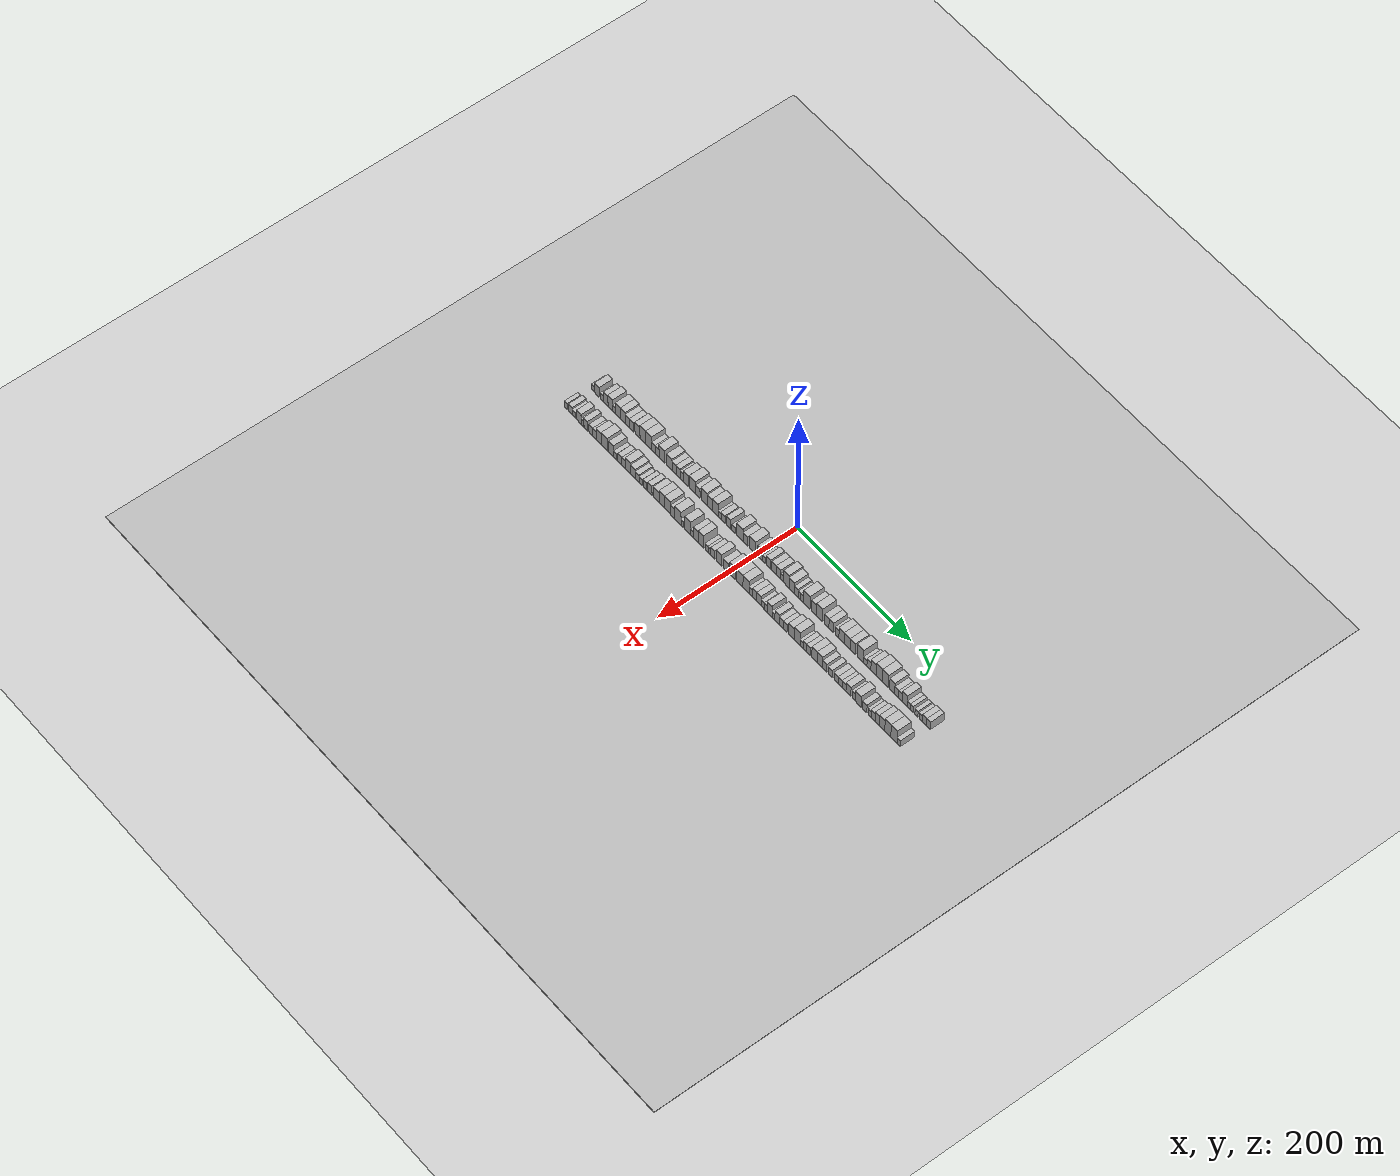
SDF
<?xml version="1.0" encoding="utf-8"?>

<sdf version="1.6">

   <world name="default">

      <gui fullscreen="0">

         <camera name="user_camera">

            <pose>-15 0 4.57585 0 0 0</pose>

            <view_controller>orbit</view_controller>

         </camera>

      </gui>

      <scene>

         <sky>

           <clouds>

             <speed>12</speed>

           </clouds>

         </sky>

         <ambient>0.4 0.4 0.4 1</ambient>

         <background>0.7 0.7 0.7 1</background>

         <shadows>1</shadows>

      </scene>

      <gravity>0 0 -9.8066</gravity>

      <magnetic_field>6e-06 2.3e-05 -4.2e-05</magnetic_field>

      <physics default="0" name="default_physics" type="ode">

         <ode>

            <solver>

               <type>quick</type>

               <iters>10</iters>

               <sor>1.0</sor>

               <use_dynamic_moi_rescaling>0</use_dynamic_moi_rescaling>

            </solver>

            <constraints>

               <cfm>0</cfm>

               <erp>0.2</erp>

               <contact_max_correcting_vel>100</contact_max_correcting_vel>

               <contact_surface_layer>0.001</contact_surface_layer>

            </constraints>

         </ode>

         <max_step_size>0.004</max_step_size>

         <real_time_factor>1</real_time_factor>

         <real_time_update_rate>250</real_time_update_rate>

      </physics>

      <light name="sun" type="directional">

         <cast_shadows>1</cast_shadows>

         <pose>0 0 10 0 0 0</pose>

         <diffuse>0.8 0.8 0.8 1</diffuse>

         <specular>0.2 0.2 0.2 1</specular>

         <attenuation>

            <range>1000</range>

            <constant>0.9</constant>

            <linear>0.01</linear>

            <quadratic>0.001</quadratic>

         </attenuation>

         <direction>-0.5 0.1 -0.9</direction>

      </light>

      <include>

         <name>ground_plane_1</name>

         <uri>model://HANNAS_ground_plane</uri>

         <pose>0 0 0  0 0 0</pose>

      </include>

      <include>

         <name>ground_plane_2</name>

         <uri>model://HANNAS_ground_plane</uri>

         <pose>100 0 0  0 0 0</pose>

      </include>

      <model name="building_1">

         <static>1</static>

         <pose frame="">50.0000 -297.5715 0 0.000000 0.000000 0.000000</pose>

         <link name="link">

            <pose frame="">0 0 6.00 0 0 0</pose>

            <collision name="collision">

               <geometry>

                  <box>

                     <size>20.0000 4.8570 12.0000</size>

                  </box>

               </geometry>

               <max_contacts>10</max_contacts>

               <surface>

                  <contact>

                     <ode/>

                  </contact>

                  <bounce/>

                  <friction>

                     <torsional>

                        <ode/>

                     </torsional>

                     <ode/>

                  </friction>

               </surface>

            </collision>

            <visual name="visual">

               <cast_shadows>0</cast_shadows>

               <geometry>

                  <box>

                     <size>20.0000 4.8570 12.0000</size>

                  </box>

               </geometry>

               <material>

                  <script>

                     <uri>model://HANNAS_wall/materials/scripts</uri>

                     <uri>model://HANNAS_wall/materials/textures</uri>

                     <name>vrc/HANNAS_wall</name>

                  </script>

               </material>

            </visual>

            <self_collide>0</self_collide>

            <enable_wind>0</enable_wind>

            <kinematic>0</kinematic>

         </link>

      </model>

      <model name="building_2">

         <static>1</static>

         <pose frame="">50.0000 -290.7994 0 0.000000 0.000000 0.000000</pose>

         <link name="link">

            <pose frame="">0 0 9.00 0 0 0</pose>

            <collision name="collision">

               <geometry>

                  <box>

                     <size>20.0000 8.6872 18.0000</size>

                  </box>

               </geometry>

               <max_contacts>10</max_contacts>

               <surface>

                  <contact>

                     <ode/>

                  </contact>

                  <bounce/>

                  <friction>

                     <torsional>

                        <ode/>

                     </torsional>

                     <ode/>

                  </friction>

               </surface>

            </collision>

            <visual name="visual">

               <cast_shadows>0</cast_shadows>

               <geometry>

                  <box>

                     <size>20.0000 8.6872 18.0000</size>

                  </box>

               </geometry>

               <material>

                  <script>

                     <uri>model://HANNAS_wall/materials/scripts</uri>

                     <uri>model://HANNAS_wall/materials/textures</uri>

                     <name>vrc/HANNAS_wall</name>

                  </script>

               </material>

            </visual>

            <self_collide>0</self_collide>

            <enable_wind>0</enable_wind>

            <kinematic>0</kinematic>

         </link>

      </model>

      <model name="building_3">

         <static>1</static>

         <pose frame="">50.0000 -280.9802 0 0.000000 0.000000 0.000000</pose>

         <link name="link">

            <pose frame="">0 0 6.00 0 0 0</pose>

            <collision name="collision">

               <geometry>

                  <box>

                     <size>20.0000 4.9514 12.0000</size>

                  </box>

               </geometry>

               <max_contacts>10</max_contacts>

               <surface>

                  <contact>

                     <ode/>

                  </contact>

                  <bounce/>

                  <friction>

                     <torsional>

                        <ode/>

                     </torsional>

                     <ode/>

                  </friction>

               </surface>

            </collision>

            <visual name="visual">

               <cast_shadows>0</cast_shadows>

               <geometry>

                  <box>

                     <size>20.0000 4.9514 12.0000</size>

                  </box>

               </geometry>

               <material>

                  <script>

                     <uri>model://HANNAS_wall/materials/scripts</uri>

                     <uri>model://HANNAS_wall/materials/textures</uri>

                     <name>vrc/HANNAS_wall</name>

                  </script>

               </material>

            </visual>

            <self_collide>0</self_collide>

            <enable_wind>0</enable_wind>

            <kinematic>0</kinematic>

         </link>

      </model>

      <model name="building_4">

         <static>1</static>

         <pose frame="">50.0000 -274.3003 0 0.000000 0.000000 0.000000</pose>

         <link name="link">

            <pose frame="">0 0 9.00 0 0 0</pose>

            <collision name="collision">

               <geometry>

                  <box>

                     <size>20.0000 8.4084 18.0000</size>

                  </box>

               </geometry>

               <max_contacts>10</max_contacts>

               <surface>

                  <contact>

                     <ode/>

                  </contact>

                  <bounce/>

                  <friction>

                     <torsional>

                        <ode/>

                     </torsional>

                     <ode/>

                  </friction>

               </surface>

            </collision>

            <visual name="visual">

               <cast_shadows>0</cast_shadows>

               <geometry>

                  <box>

                     <size>20.0000 8.4084 18.0000</size>

                  </box>

               </geometry>

               <material>

                  <script>

                     <uri>model://HANNAS_wall/materials/scripts</uri>

                     <uri>model://HANNAS_wall/materials/textures</uri>

                     <name>vrc/HANNAS_wall</name>

                  </script>

               </material>

            </visual>

            <self_collide>0</self_collide>

            <enable_wind>0</enable_wind>

            <kinematic>0</kinematic>

         </link>

      </model>

      <model name="building_5">

         <static>1</static>

         <pose frame="">50.0000 -265.5569 0 0.000000 0.000000 0.000000</pose>

         <link name="link">

            <pose frame="">0 0 10.50 0 0 0</pose>

            <collision name="collision">

               <geometry>

                  <box>

                     <size>20.0000 9.0783 21.0000</size>

                  </box>

               </geometry>

               <max_contacts>10</max_contacts>

               <surface>

                  <contact>

                     <ode/>

                  </contact>

                  <bounce/>

                  <friction>

                     <torsional>

                        <ode/>

                     </torsional>

                     <ode/>

                  </friction>

               </surface>

            </collision>

            <visual name="visual">

               <cast_shadows>0</cast_shadows>

               <geometry>

                  <box>

                     <size>20.0000 9.0783 21.0000</size>

                  </box>

               </geometry>

               <material>

                  <script>

                     <uri>model://HANNAS_wall/materials/scripts</uri>

                     <uri>model://HANNAS_wall/materials/textures</uri>

                     <name>vrc/HANNAS_wall</name>

                  </script>

               </material>

            </visual>

            <self_collide>0</self_collide>

            <enable_wind>0</enable_wind>

            <kinematic>0</kinematic>

         </link>

      </model>

      <model name="building_6">

         <static>1</static>

         <pose frame="">50.0000 -258.6084 0 0.000000 0.000000 0.000000</pose>

         <link name="link">

            <pose frame="">0 0 6.00 0 0 0</pose>

            <collision name="collision">

               <geometry>

                  <box>

                     <size>20.0000 4.8188 12.0000</size>

                  </box>

               </geometry>

               <max_contacts>10</max_contacts>

               <surface>

                  <contact>

                     <ode/>

                  </contact>

                  <bounce/>

                  <friction>

                     <torsional>

                        <ode/>

                     </torsional>

                     <ode/>

                  </friction>

               </surface>

            </collision>

            <visual name="visual">

               <cast_shadows>0</cast_shadows>

               <geometry>

                  <box>

                     <size>20.0000 4.8188 12.0000</size>

                  </box>

               </geometry>

               <material>

                  <script>

                     <uri>model://HANNAS_wall/materials/scripts</uri>

                     <uri>model://HANNAS_wall/materials/textures</uri>

                     <name>vrc/HANNAS_wall</name>

                  </script>

               </material>

            </visual>

            <self_collide>0</self_collide>

            <enable_wind>0</enable_wind>

            <kinematic>0</kinematic>

         </link>

      </model>

      <model name="building_7">

         <static>1</static>

         <pose frame="">50.0000 -251.3825 0 0.000000 0.000000 0.000000</pose>

         <link name="link">

            <pose frame="">0 0 10.50 0 0 0</pose>

            <collision name="collision">

               <geometry>

                  <box>

                     <size>20.0000 9.6330 21.0000</size>

                  </box>

               </geometry>

               <max_contacts>10</max_contacts>

               <surface>

                  <contact>

                     <ode/>

                  </contact>

                  <bounce/>

                  <friction>

                     <torsional>

                        <ode/>

                     </torsional>

                     <ode/>

                  </friction>

               </surface>

            </collision>

            <visual name="visual">

               <cast_shadows>0</cast_shadows>

               <geometry>

                  <box>

                     <size>20.0000 9.6330 21.0000</size>

                  </box>

               </geometry>

               <material>

                  <script>

                     <uri>model://HANNAS_wall/materials/scripts</uri>

                     <uri>model://HANNAS_wall/materials/textures</uri>

                     <name>vrc/HANNAS_wall</name>

                  </script>

               </material>

            </visual>

            <self_collide>0</self_collide>

            <enable_wind>0</enable_wind>

            <kinematic>0</kinematic>

         </link>

      </model>

      <model name="building_8">

         <static>1</static>

         <pose frame="">50.0000 -242.0816 0 0.000000 0.000000 0.000000</pose>

         <link name="link">

            <pose frame="">0 0 10.50 0 0 0</pose>

            <collision name="collision">

               <geometry>

                  <box>

                     <size>20.0000 8.9687 21.0000</size>

                  </box>

               </geometry>

               <max_contacts>10</max_contacts>

               <surface>

                  <contact>

                     <ode/>

                  </contact>

                  <bounce/>

                  <friction>

                     <torsional>

                        <ode/>

                     </torsional>

                     <ode/>

                  </friction>

               </surface>

            </collision>

            <visual name="visual">

               <cast_shadows>0</cast_shadows>

               <geometry>

                  <box>

                     <size>20.0000 8.9687 21.0000</size>

                  </box>

               </geometry>

               <material>

                  <script>

                     <uri>model://HANNAS_wall/materials/scripts</uri>

                     <uri>model://HANNAS_wall/materials/textures</uri>

                     <name>vrc/HANNAS_wall</name>

                  </script>

               </material>

            </visual>

            <self_collide>0</self_collide>

            <enable_wind>0</enable_wind>

            <kinematic>0</kinematic>

         </link>

      </model>

      <model name="building_9">

         <static>1</static>

         <pose frame="">50.0000 -233.7496 0 0.000000 0.000000 0.000000</pose>

         <link name="link">

            <pose frame="">0 0 9.00 0 0 0</pose>

            <collision name="collision">

               <geometry>

                  <box>

                     <size>20.0000 7.6954 18.0000</size>

                  </box>

               </geometry>

               <max_contacts>10</max_contacts>

               <surface>

                  <contact>

                     <ode/>

                  </contact>

                  <bounce/>

                  <friction>

                     <torsional>

                        <ode/>

                     </torsional>

                     <ode/>

                  </friction>

               </surface>

            </collision>

            <visual name="visual">

               <cast_shadows>0</cast_shadows>

               <geometry>

                  <box>

                     <size>20.0000 7.6954 18.0000</size>

                  </box>

               </geometry>

               <material>

                  <script>

                     <uri>model://HANNAS_wall/materials/scripts</uri>

                     <uri>model://HANNAS_wall/materials/textures</uri>

                     <name>vrc/HANNAS_wall</name>

                  </script>

               </material>

            </visual>

            <self_collide>0</self_collide>

            <enable_wind>0</enable_wind>

            <kinematic>0</kinematic>

         </link>

      </model>

      <model name="building_10">

         <static>1</static>

         <pose frame="">50.0000 -226.0455 0 0.000000 0.000000 0.000000</pose>

         <link name="link">

            <pose frame="">0 0 9.00 0 0 0</pose>

            <collision name="collision">

               <geometry>

                  <box>

                     <size>20.0000 7.7126 18.0000</size>

                  </box>

               </geometry>

               <max_contacts>10</max_contacts>

               <surface>

                  <contact>

                     <ode/>

                  </contact>

                  <bounce/>

                  <friction>

                     <torsional>

                        <ode/>

                     </torsional>

                     <ode/>

                  </friction>

               </surface>

            </collision>

            <visual name="visual">

               <cast_shadows>0</cast_shadows>

               <geometry>

                  <box>

                     <size>20.0000 7.7126 18.0000</size>

                  </box>

               </geometry>

               <material>

                  <script>

                     <uri>model://HANNAS_wall/materials/scripts</uri>

                     <uri>model://HANNAS_wall/materials/textures</uri>

                     <name>vrc/HANNAS_wall</name>

                  </script>

               </material>

            </visual>

            <self_collide>0</self_collide>

            <enable_wind>0</enable_wind>

            <kinematic>0</kinematic>

         </link>

      </model>

      <model name="building_11">

         <static>1</static>

         <pose frame="">50.0000 -215.5581 0 0.000000 0.000000 0.000000</pose>

         <link name="link">

            <pose frame="">0 0 10.50 0 0 0</pose>

            <collision name="collision">

               <geometry>

                  <box>

                     <size>20.0000 9.2623 21.0000</size>

                  </box>

               </geometry>

               <max_contacts>10</max_contacts>

               <surface>

                  <contact>

                     <ode/>

                  </contact>

                  <bounce/>

                  <friction>

                     <torsional>

                        <ode/>

                     </torsional>

                     <ode/>

                  </friction>

               </surface>

            </collision>

            <visual name="visual">

               <cast_shadows>0</cast_shadows>

               <geometry>

                  <box>

                     <size>20.0000 9.2623 21.0000</size>

                  </box>

               </geometry>

               <material>

                  <script>

                     <uri>model://HANNAS_wall/materials/scripts</uri>

                     <uri>model://HANNAS_wall/materials/textures</uri>

                     <name>vrc/HANNAS_wall</name>

                  </script>

               </material>

            </visual>

            <self_collide>0</self_collide>

            <enable_wind>0</enable_wind>

            <kinematic>0</kinematic>

         </link>

      </model>

      <model name="building_12">

         <static>1</static>

         <pose frame="">50.0000 -205.7762 0 0.000000 0.000000 0.000000</pose>

         <link name="link">

            <pose frame="">0 0 12.00 0 0 0</pose>

            <collision name="collision">

               <geometry>

                  <box>

                     <size>20.0000 10.3015 24.0000</size>

                  </box>

               </geometry>

               <max_contacts>10</max_contacts>

               <surface>

                  <contact>

                     <ode/>

                  </contact>

                  <bounce/>

                  <friction>

                     <torsional>

                        <ode/>

                     </torsional>

                     <ode/>

                  </friction>

               </surface>

            </collision>

            <visual name="visual">

               <cast_shadows>0</cast_shadows>

               <geometry>

                  <box>

                     <size>20.0000 10.3015 24.0000</size>

                  </box>

               </geometry>

               <material>

                  <script>

                     <uri>model://HANNAS_wall/materials/scripts</uri>

                     <uri>model://HANNAS_wall/materials/textures</uri>

                     <name>vrc/HANNAS_wall</name>

                  </script>

               </material>

            </visual>

            <self_collide>0</self_collide>

            <enable_wind>0</enable_wind>

            <kinematic>0</kinematic>

         </link>

      </model>

      <model name="building_13">

         <static>1</static>

         <pose frame="">50.0000 -195.0669 0 0.000000 0.000000 0.000000</pose>

         <link name="link">

            <pose frame="">0 0 12.00 0 0 0</pose>

            <collision name="collision">

               <geometry>

                  <box>

                     <size>20.0000 11.1171 24.0000</size>

                  </box>

               </geometry>

               <max_contacts>10</max_contacts>

               <surface>

                  <contact>

                     <ode/>

                  </contact>

                  <bounce/>

                  <friction>

                     <torsional>

                        <ode/>

                     </torsional>

                     <ode/>

                  </friction>

               </surface>

            </collision>

            <visual name="visual">

               <cast_shadows>0</cast_shadows>

               <geometry>

                  <box>

                     <size>20.0000 11.1171 24.0000</size>

                  </box>

               </geometry>

               <material>

                  <script>

                     <uri>model://HANNAS_wall/materials/scripts</uri>

                     <uri>model://HANNAS_wall/materials/textures</uri>

                     <name>vrc/HANNAS_wall</name>

                  </script>

               </material>

            </visual>

            <self_collide>0</self_collide>

            <enable_wind>0</enable_wind>

            <kinematic>0</kinematic>

         </link>

      </model>

      <model name="building_14">

         <static>1</static>

         <pose frame="">50.0000 -186.2584 0 0.000000 0.000000 0.000000</pose>

         <link name="link">

            <pose frame="">0 0 7.50 0 0 0</pose>

            <collision name="collision">

               <geometry>

                  <box>

                     <size>20.0000 6.4999 15.0000</size>

                  </box>

               </geometry>

               <max_contacts>10</max_contacts>

               <surface>

                  <contact>

                     <ode/>

                  </contact>

                  <bounce/>

                  <friction>

                     <torsional>

                        <ode/>

                     </torsional>

                     <ode/>

                  </friction>

               </surface>

            </collision>

            <visual name="visual">

               <cast_shadows>0</cast_shadows>

               <geometry>

                  <box>

                     <size>20.0000 6.4999 15.0000</size>

                  </box>

               </geometry>

               <material>

                  <script>

                     <uri>model://HANNAS_wall/materials/scripts</uri>

                     <uri>model://HANNAS_wall/materials/textures</uri>

                     <name>vrc/HANNAS_wall</name>

                  </script>

               </material>

            </visual>

            <self_collide>0</self_collide>

            <enable_wind>0</enable_wind>

            <kinematic>0</kinematic>

         </link>

      </model>

      <model name="building_15">

         <static>1</static>

         <pose frame="">50.0000 -179.4305 0 0.000000 0.000000 0.000000</pose>

         <link name="link">

            <pose frame="">0 0 7.50 0 0 0</pose>

            <collision name="collision">

               <geometry>

                  <box>

                     <size>20.0000 7.1558 15.0000</size>

                  </box>

               </geometry>

               <max_contacts>10</max_contacts>

               <surface>

                  <contact>

                     <ode/>

                  </contact>

                  <bounce/>

                  <friction>

                     <torsional>

                        <ode/>

                     </torsional>

                     <ode/>

                  </friction>

               </surface>

            </collision>

            <visual name="visual">

               <cast_shadows>0</cast_shadows>

               <geometry>

                  <box>

                     <size>20.0000 7.1558 15.0000</size>

                  </box>

               </geometry>

               <material>

                  <script>

                     <uri>model://HANNAS_wall/materials/scripts</uri>

                     <uri>model://HANNAS_wall/materials/textures</uri>

                     <name>vrc/HANNAS_wall</name>

                  </script>

               </material>

            </visual>

            <self_collide>0</self_collide>

            <enable_wind>0</enable_wind>

            <kinematic>0</kinematic>

         </link>

      </model>

      <model name="building_16">

         <static>1</static>

         <pose frame="">50.0000 -170.4923 0 0.000000 0.000000 0.000000</pose>

         <link name="link">

            <pose frame="">0 0 12.00 0 0 0</pose>

            <collision name="collision">

               <geometry>

                  <box>

                     <size>20.0000 10.7208 24.0000</size>

                  </box>

               </geometry>

               <max_contacts>10</max_contacts>

               <surface>

                  <contact>

                     <ode/>

                  </contact>

                  <bounce/>

                  <friction>

                     <torsional>

                        <ode/>

                     </torsional>

                     <ode/>

                  </friction>

               </surface>

            </collision>

            <visual name="visual">

               <cast_shadows>0</cast_shadows>

               <geometry>

                  <box>

                     <size>20.0000 10.7208 24.0000</size>

                  </box>

               </geometry>

               <material>

                  <script>

                     <uri>model://HANNAS_wall/materials/scripts</uri>

                     <uri>model://HANNAS_wall/materials/textures</uri>

                     <name>vrc/HANNAS_wall</name>

                  </script>

               </material>

            </visual>

            <self_collide>0</self_collide>

            <enable_wind>0</enable_wind>

            <kinematic>0</kinematic>

         </link>

      </model>

      <model name="building_17">

         <static>1</static>

         <pose frame="">50.0000 -157.0809 0 0.000000 0.000000 0.000000</pose>

         <link name="link">

            <pose frame="">0 0 10.50 0 0 0</pose>

            <collision name="collision">

               <geometry>

                  <box>

                     <size>20.0000 10.1021 21.0000</size>

                  </box>

               </geometry>

               <max_contacts>10</max_contacts>

               <surface>

                  <contact>

                     <ode/>

                  </contact>

                  <bounce/>

                  <friction>

                     <torsional>

                        <ode/>

                     </torsional>

                     <ode/>

                  </friction>

               </surface>

            </collision>

            <visual name="visual">

               <cast_shadows>0</cast_shadows>

               <geometry>

                  <box>

                     <size>20.0000 10.1021 21.0000</size>

                  </box>

               </geometry>

               <material>

                  <script>

                     <uri>model://HANNAS_wall/materials/scripts</uri>

                     <uri>model://HANNAS_wall/materials/textures</uri>

                     <name>vrc/HANNAS_wall</name>

                  </script>

               </material>

            </visual>

            <self_collide>0</self_collide>

            <enable_wind>0</enable_wind>

            <kinematic>0</kinematic>

         </link>

      </model>

      <model name="building_18">

         <static>1</static>

         <pose frame="">50.0000 -148.2817 0 0.000000 0.000000 0.000000</pose>

         <link name="link">

            <pose frame="">0 0 9.00 0 0 0</pose>

            <collision name="collision">

               <geometry>

                  <box>

                     <size>20.0000 7.4962 18.0000</size>

                  </box>

               </geometry>

               <max_contacts>10</max_contacts>

               <surface>

                  <contact>

                     <ode/>

                  </contact>

                  <bounce/>

                  <friction>

                     <torsional>

                        <ode/>

                     </torsional>

                     <ode/>

                  </friction>

               </surface>

            </collision>

            <visual name="visual">

               <cast_shadows>0</cast_shadows>

               <geometry>

                  <box>

                     <size>20.0000 7.4962 18.0000</size>

                  </box>

               </geometry>

               <material>

                  <script>

                     <uri>model://HANNAS_wall/materials/scripts</uri>

                     <uri>model://HANNAS_wall/materials/textures</uri>

                     <name>vrc/HANNAS_wall</name>

                  </script>

               </material>

            </visual>

            <self_collide>0</self_collide>

            <enable_wind>0</enable_wind>

            <kinematic>0</kinematic>

         </link>

      </model>

      <model name="building_19">

         <static>1</static>

         <pose frame="">50.0000 -140.9135 0 0.000000 0.000000 0.000000</pose>

         <link name="link">

            <pose frame="">0 0 9.00 0 0 0</pose>

            <collision name="collision">

               <geometry>

                  <box>

                     <size>20.0000 7.2403 18.0000</size>

                  </box>

               </geometry>

               <max_contacts>10</max_contacts>

               <surface>

                  <contact>

                     <ode/>

                  </contact>

                  <bounce/>

                  <friction>

                     <torsional>

                        <ode/>

                     </torsional>

                     <ode/>

                  </friction>

               </surface>

            </collision>

            <visual name="visual">

               <cast_shadows>0</cast_shadows>

               <geometry>

                  <box>

                     <size>20.0000 7.2403 18.0000</size>

                  </box>

               </geometry>

               <material>

                  <script>

                     <uri>model://HANNAS_wall/materials/scripts</uri>

                     <uri>model://HANNAS_wall/materials/textures</uri>

                     <name>vrc/HANNAS_wall</name>

                  </script>

               </material>

            </visual>

            <self_collide>0</self_collide>

            <enable_wind>0</enable_wind>

            <kinematic>0</kinematic>

         </link>

      </model>

      <model name="building_20">

         <static>1</static>

         <pose frame="">50.0000 -134.1900 0 0.000000 0.000000 0.000000</pose>

         <link name="link">

            <pose frame="">0 0 7.50 0 0 0</pose>

            <collision name="collision">

               <geometry>

                  <box>

                     <size>20.0000 6.2068 15.0000</size>

                  </box>

               </geometry>

               <max_contacts>10</max_contacts>

               <surface>

                  <contact>

                     <ode/>

                  </contact>

                  <bounce/>

                  <friction>

                     <torsional>

                        <ode/>

                     </torsional>

                     <ode/>

                  </friction>

               </surface>

            </collision>

            <visual name="visual">

               <cast_shadows>0</cast_shadows>

               <geometry>

                  <box>

                     <size>20.0000 6.2068 15.0000</size>

                  </box>

               </geometry>

               <material>

                  <script>

                     <uri>model://HANNAS_wall/materials/scripts</uri>

                     <uri>model://HANNAS_wall/materials/textures</uri>

                     <name>vrc/HANNAS_wall</name>

                  </script>

               </material>

            </visual>

            <self_collide>0</self_collide>

            <enable_wind>0</enable_wind>

            <kinematic>0</kinematic>

         </link>

      </model>

      <model name="building_21">

         <static>1</static>

         <pose frame="">50.0000 -126.5503 0 0.000000 0.000000 0.000000</pose>

         <link name="link">

            <pose frame="">0 0 10.50 0 0 0</pose>

            <collision name="collision">

               <geometry>

                  <box>

                     <size>20.0000 9.0725 21.0000</size>

                  </box>

               </geometry>

               <max_contacts>10</max_contacts>

               <surface>

                  <contact>

                     <ode/>

                  </contact>

                  <bounce/>

                  <friction>

                     <torsional>

                        <ode/>

                     </torsional>

                     <ode/>

                  </friction>

               </surface>

            </collision>

            <visual name="visual">

               <cast_shadows>0</cast_shadows>

               <geometry>

                  <box>

                     <size>20.0000 9.0725 21.0000</size>

                  </box>

               </geometry>

               <material>

                  <script>

                     <uri>model://HANNAS_wall/materials/scripts</uri>

                     <uri>model://HANNAS_wall/materials/textures</uri>

                     <name>vrc/HANNAS_wall</name>

                  </script>

               </material>

            </visual>

            <self_collide>0</self_collide>

            <enable_wind>0</enable_wind>

            <kinematic>0</kinematic>

         </link>

      </model>

      <model name="building_22">

         <static>1</static>

         <pose frame="">50.0000 -114.3188 0 0.000000 0.000000 0.000000</pose>

         <link name="link">

            <pose frame="">0 0 12.00 0 0 0</pose>

            <collision name="collision">

               <geometry>

                  <box>

                     <size>20.0000 11.3905 24.0000</size>

                  </box>

               </geometry>

               <max_contacts>10</max_contacts>

               <surface>

                  <contact>

                     <ode/>

                  </contact>

                  <bounce/>

                  <friction>

                     <torsional>

                        <ode/>

                     </torsional>

                     <ode/>

                  </friction>

               </surface>

            </collision>

            <visual name="visual">

               <cast_shadows>0</cast_shadows>

               <geometry>

                  <box>

                     <size>20.0000 11.3905 24.0000</size>

                  </box>

               </geometry>

               <material>

                  <script>

                     <uri>model://HANNAS_wall/materials/scripts</uri>

                     <uri>model://HANNAS_wall/materials/textures</uri>

                     <name>vrc/HANNAS_wall</name>

                  </script>

               </material>

            </visual>

            <self_collide>0</self_collide>

            <enable_wind>0</enable_wind>

            <kinematic>0</kinematic>

         </link>

      </model>

      <model name="building_23">

         <static>1</static>

         <pose frame="">50.0000 -104.8672 0 0.000000 0.000000 0.000000</pose>

         <link name="link">

            <pose frame="">0 0 9.00 0 0 0</pose>

            <collision name="collision">

               <geometry>

                  <box>

                     <size>20.0000 7.5128 18.0000</size>

                  </box>

               </geometry>

               <max_contacts>10</max_contacts>

               <surface>

                  <contact>

                     <ode/>

                  </contact>

                  <bounce/>

                  <friction>

                     <torsional>

                        <ode/>

                     </torsional>

                     <ode/>

                  </friction>

               </surface>

            </collision>

            <visual name="visual">

               <cast_shadows>0</cast_shadows>

               <geometry>

                  <box>

                     <size>20.0000 7.5128 18.0000</size>

                  </box>

               </geometry>

               <material>

                  <script>

                     <uri>model://HANNAS_wall/materials/scripts</uri>

                     <uri>model://HANNAS_wall/materials/textures</uri>

                     <name>vrc/HANNAS_wall</name>

                  </script>

               </material>

            </visual>

            <self_collide>0</self_collide>

            <enable_wind>0</enable_wind>

            <kinematic>0</kinematic>

         </link>

      </model>

      <model name="building_24">

         <static>1</static>

         <pose frame="">50.0000 -93.4741 0 0.000000 0.000000 0.000000</pose>

         <link name="link">

            <pose frame="">0 0 12.00 0 0 0</pose>

            <collision name="collision">

               <geometry>

                  <box>

                     <size>20.0000 11.2733 24.0000</size>

                  </box>

               </geometry>

               <max_contacts>10</max_contacts>

               <surface>

                  <contact>

                     <ode/>

                  </contact>

                  <bounce/>

                  <friction>

                     <torsional>

                        <ode/>

                     </torsional>

                     <ode/>

                  </friction>

               </surface>

            </collision>

            <visual name="visual">

               <cast_shadows>0</cast_shadows>

               <geometry>

                  <box>

                     <size>20.0000 11.2733 24.0000</size>

                  </box>

               </geometry>

               <material>

                  <script>

                     <uri>model://HANNAS_wall/materials/scripts</uri>

                     <uri>model://HANNAS_wall/materials/textures</uri>

                     <name>vrc/HANNAS_wall</name>

                  </script>

               </material>

            </visual>

            <self_collide>0</self_collide>

            <enable_wind>0</enable_wind>

            <kinematic>0</kinematic>

         </link>

      </model>

      <model name="building_25">

         <static>1</static>

         <pose frame="">50.0000 -82.9544 0 0.000000 0.000000 0.000000</pose>

         <link name="link">

            <pose frame="">0 0 10.50 0 0 0</pose>

            <collision name="collision">

               <geometry>

                  <box>

                     <size>20.0000 9.7661 21.0000</size>

                  </box>

               </geometry>

               <max_contacts>10</max_contacts>

               <surface>

                  <contact>

                     <ode/>

                  </contact>

                  <bounce/>

                  <friction>

                     <torsional>

                        <ode/>

                     </torsional>

                     <ode/>

                  </friction>

               </surface>

            </collision>

            <visual name="visual">

               <cast_shadows>0</cast_shadows>

               <geometry>

                  <box>

                     <size>20.0000 9.7661 21.0000</size>

                  </box>

               </geometry>

               <material>

                  <script>

                     <uri>model://HANNAS_wall/materials/scripts</uri>

                     <uri>model://HANNAS_wall/materials/textures</uri>

                     <name>vrc/HANNAS_wall</name>

                  </script>

               </material>

            </visual>

            <self_collide>0</self_collide>

            <enable_wind>0</enable_wind>

            <kinematic>0</kinematic>

         </link>

      </model>

      <model name="building_26">

         <static>1</static>

         <pose frame="">50.0000 -73.1143 0 0.000000 0.000000 0.000000</pose>

         <link name="link">

            <pose frame="">0 0 12.00 0 0 0</pose>

            <collision name="collision">

               <geometry>

                  <box>

                     <size>20.0000 9.9142 24.0000</size>

                  </box>

               </geometry>

               <max_contacts>10</max_contacts>

               <surface>

                  <contact>

                     <ode/>

                  </contact>

                  <bounce/>

                  <friction>

                     <torsional>

                        <ode/>

                     </torsional>

                     <ode/>

                  </friction>

               </surface>

            </collision>

            <visual name="visual">

               <cast_shadows>0</cast_shadows>

               <geometry>

                  <box>

                     <size>20.0000 9.9142 24.0000</size>

                  </box>

               </geometry>

               <material>

                  <script>

                     <uri>model://HANNAS_wall/materials/scripts</uri>

                     <uri>model://HANNAS_wall/materials/textures</uri>

                     <name>vrc/HANNAS_wall</name>

                  </script>

               </material>

            </visual>

            <self_collide>0</self_collide>

            <enable_wind>0</enable_wind>

            <kinematic>0</kinematic>

         </link>

      </model>

      <model name="building_27">

         <static>1</static>

         <pose frame="">50.0000 -65.5913 0 0.000000 0.000000 0.000000</pose>

         <link name="link">

            <pose frame="">0 0 6.00 0 0 0</pose>

            <collision name="collision">

               <geometry>

                  <box>

                     <size>20.0000 5.1318 12.0000</size>

                  </box>

               </geometry>

               <max_contacts>10</max_contacts>

               <surface>

                  <contact>

                     <ode/>

                  </contact>

                  <bounce/>

                  <friction>

                     <torsional>

                        <ode/>

                     </torsional>

                     <ode/>

                  </friction>

               </surface>

            </collision>

            <visual name="visual">

               <cast_shadows>0</cast_shadows>

               <geometry>

                  <box>

                     <size>20.0000 5.1318 12.0000</size>

                  </box>

               </geometry>

               <material>

                  <script>

                     <uri>model://HANNAS_wall/materials/scripts</uri>

                     <uri>model://HANNAS_wall/materials/textures</uri>

                     <name>vrc/HANNAS_wall</name>

                  </script>

               </material>

            </visual>

            <self_collide>0</self_collide>

            <enable_wind>0</enable_wind>

            <kinematic>0</kinematic>

         </link>

      </model>

      <model name="building_28">

         <static>1</static>

         <pose frame="">50.0000 -59.3571 0 0.000000 0.000000 0.000000</pose>

         <link name="link">

            <pose frame="">0 0 7.50 0 0 0</pose>

            <collision name="collision">

               <geometry>

                  <box>

                     <size>20.0000 7.3364 15.0000</size>

                  </box>

               </geometry>

               <max_contacts>10</max_contacts>

               <surface>

                  <contact>

                     <ode/>

                  </contact>

                  <bounce/>

                  <friction>

                     <torsional>

                        <ode/>

                     </torsional>

                     <ode/>

                  </friction>

               </surface>

            </collision>

            <visual name="visual">

               <cast_shadows>0</cast_shadows>

               <geometry>

                  <box>

                     <size>20.0000 7.3364 15.0000</size>

                  </box>

               </geometry>

               <material>

                  <script>

                     <uri>model://HANNAS_wall/materials/scripts</uri>

                     <uri>model://HANNAS_wall/materials/textures</uri>

                     <name>vrc/HANNAS_wall</name>

                  </script>

               </material>

            </visual>

            <self_collide>0</self_collide>

            <enable_wind>0</enable_wind>

            <kinematic>0</kinematic>

         </link>

      </model>

      <model name="building_29">

         <static>1</static>

         <pose frame="">50.0000 -49.0608 0 0.000000 0.000000 0.000000</pose>

         <link name="link">

            <pose frame="">0 0 9.00 0 0 0</pose>

            <collision name="collision">

               <geometry>

                  <box>

                     <size>20.0000 7.2563 18.0000</size>

                  </box>

               </geometry>

               <max_contacts>10</max_contacts>

               <surface>

                  <contact>

                     <ode/>

                  </contact>

                  <bounce/>

                  <friction>

                     <torsional>

                        <ode/>

                     </torsional>

                     <ode/>

                  </friction>

               </surface>

            </collision>

            <visual name="visual">

               <cast_shadows>0</cast_shadows>

               <geometry>

                  <box>

                     <size>20.0000 7.2563 18.0000</size>

                  </box>

               </geometry>

               <material>

                  <script>

                     <uri>model://HANNAS_wall/materials/scripts</uri>

                     <uri>model://HANNAS_wall/materials/textures</uri>

                     <name>vrc/HANNAS_wall</name>

                  </script>

               </material>

            </visual>

            <self_collide>0</self_collide>

            <enable_wind>0</enable_wind>

            <kinematic>0</kinematic>

         </link>

      </model>

      <model name="building_30">

         <static>1</static>

         <pose frame="">50.0000 -40.4750 0 0.000000 0.000000 0.000000</pose>

         <link name="link">

            <pose frame="">0 0 6.00 0 0 0</pose>

            <collision name="collision">

               <geometry>

                  <box>

                     <size>20.0000 5.9151 12.0000</size>

                  </box>

               </geometry>

               <max_contacts>10</max_contacts>

               <surface>

                  <contact>

                     <ode/>

                  </contact>

                  <bounce/>

                  <friction>

                     <torsional>

                        <ode/>

                     </torsional>

                     <ode/>

                  </friction>

               </surface>

            </collision>

            <visual name="visual">

               <cast_shadows>0</cast_shadows>

               <geometry>

                  <box>

                     <size>20.0000 5.9151 12.0000</size>

                  </box>

               </geometry>

               <material>

                  <script>

                     <uri>model://HANNAS_wall/materials/scripts</uri>

                     <uri>model://HANNAS_wall/materials/textures</uri>

                     <name>vrc/HANNAS_wall</name>

                  </script>

               </material>

            </visual>

            <self_collide>0</self_collide>

            <enable_wind>0</enable_wind>

            <kinematic>0</kinematic>

         </link>

      </model>

      <model name="building_31">

         <static>1</static>

         <pose frame="">50.0000 -28.9358 0 0.000000 0.000000 0.000000</pose>

         <link name="link">

            <pose frame="">0 0 12.00 0 0 0</pose>

            <collision name="collision">

               <geometry>

                  <box>

                     <size>20.0000 11.1633 24.0000</size>

                  </box>

               </geometry>

               <max_contacts>10</max_contacts>

               <surface>

                  <contact>

                     <ode/>

                  </contact>

                  <bounce/>

                  <friction>

                     <torsional>

                        <ode/>

                     </torsional>

                     <ode/>

                  </friction>

               </surface>

            </collision>

            <visual name="visual">

               <cast_shadows>0</cast_shadows>

               <geometry>

                  <box>

                     <size>20.0000 11.1633 24.0000</size>

                  </box>

               </geometry>

               <material>

                  <script>

                     <uri>model://HANNAS_wall/materials/scripts</uri>

                     <uri>model://HANNAS_wall/materials/textures</uri>

                     <name>vrc/HANNAS_wall</name>

                  </script>

               </material>

            </visual>

            <self_collide>0</self_collide>

            <enable_wind>0</enable_wind>

            <kinematic>0</kinematic>

         </link>

      </model>

      <model name="building_32">

         <static>1</static>

         <pose frame="">50.0000 -19.0690 0 0.000000 0.000000 0.000000</pose>

         <link name="link">

            <pose frame="">0 0 9.00 0 0 0</pose>

            <collision name="collision">

               <geometry>

                  <box>

                     <size>20.0000 8.5704 18.0000</size>

                  </box>

               </geometry>

               <max_contacts>10</max_contacts>

               <surface>

                  <contact>

                     <ode/>

                  </contact>

                  <bounce/>

                  <friction>

                     <torsional>

                        <ode/>

                     </torsional>

                     <ode/>

                  </friction>

               </surface>

            </collision>

            <visual name="visual">

               <cast_shadows>0</cast_shadows>

               <geometry>

                  <box>

                     <size>20.0000 8.5704 18.0000</size>

                  </box>

               </geometry>

               <material>

                  <script>

                     <uri>model://HANNAS_wall/materials/scripts</uri>

                     <uri>model://HANNAS_wall/materials/textures</uri>

                     <name>vrc/HANNAS_wall</name>

                  </script>

               </material>

            </visual>

            <self_collide>0</self_collide>

            <enable_wind>0</enable_wind>

            <kinematic>0</kinematic>

         </link>

      </model>

      <model name="building_33">

         <static>1</static>

         <pose frame="">50.0000 -6.0298 0 0.000000 0.000000 0.000000</pose>

         <link name="link">

            <pose frame="">0 0 12.00 0 0 0</pose>

            <collision name="collision">

               <geometry>

                  <box>

                     <size>20.0000 11.5079 24.0000</size>

                  </box>

               </geometry>

               <max_contacts>10</max_contacts>

               <surface>

                  <contact>

                     <ode/>

                  </contact>

                  <bounce/>

                  <friction>

                     <torsional>

                        <ode/>

                     </torsional>

                     <ode/>

                  </friction>

               </surface>

            </collision>

            <visual name="visual">

               <cast_shadows>0</cast_shadows>

               <geometry>

                  <box>

                     <size>20.0000 11.5079 24.0000</size>

                  </box>

               </geometry>

               <material>

                  <script>

                     <uri>model://HANNAS_wall/materials/scripts</uri>

                     <uri>model://HANNAS_wall/materials/textures</uri>

                     <name>vrc/HANNAS_wall</name>

                  </script>

               </material>

            </visual>

            <self_collide>0</self_collide>

            <enable_wind>0</enable_wind>

            <kinematic>0</kinematic>

         </link>

      </model>

      <model name="building_34">

         <static>1</static>

         <pose frame="">50.0000 7.1088 0 0.000000 0.000000 0.000000</pose>

         <link name="link">

            <pose frame="">0 0 10.50 0 0 0</pose>

            <collision name="collision">

               <geometry>

                  <box>

                     <size>20.0000 8.7692 21.0000</size>

                  </box>

               </geometry>

               <max_contacts>10</max_contacts>

               <surface>

                  <contact>

                     <ode/>

                  </contact>

                  <bounce/>

                  <friction>

                     <torsional>

                        <ode/>

                     </torsional>

                     <ode/>

                  </friction>

               </surface>

            </collision>

            <visual name="visual">

               <cast_shadows>0</cast_shadows>

               <geometry>

                  <box>

                     <size>20.0000 8.7692 21.0000</size>

                  </box>

               </geometry>

               <material>

                  <script>

                     <uri>model://HANNAS_wall/materials/scripts</uri>

                     <uri>model://HANNAS_wall/materials/textures</uri>

                     <name>vrc/HANNAS_wall</name>

                  </script>

               </material>

            </visual>

            <self_collide>0</self_collide>

            <enable_wind>0</enable_wind>

            <kinematic>0</kinematic>

         </link>

      </model>

      <model name="building_35">

         <static>1</static>

         <pose frame="">50.0000 13.9240 0 0.000000 0.000000 0.000000</pose>

         <link name="link">

            <pose frame="">0 0 6.00 0 0 0</pose>

            <collision name="collision">

               <geometry>

                  <box>

                     <size>20.0000 4.8613 12.0000</size>

                  </box>

               </geometry>

               <max_contacts>10</max_contacts>

               <surface>

                  <contact>

                     <ode/>

                  </contact>

                  <bounce/>

                  <friction>

                     <torsional>

                        <ode/>

                     </torsional>

                     <ode/>

                  </friction>

               </surface>

            </collision>

            <visual name="visual">

               <cast_shadows>0</cast_shadows>

               <geometry>

                  <box>

                     <size>20.0000 4.8613 12.0000</size>

                  </box>

               </geometry>

               <material>

                  <script>

                     <uri>model://HANNAS_wall/materials/scripts</uri>

                     <uri>model://HANNAS_wall/materials/textures</uri>

                     <name>vrc/HANNAS_wall</name>

                  </script>

               </material>

            </visual>

            <self_collide>0</self_collide>

            <enable_wind>0</enable_wind>

            <kinematic>0</kinematic>

         </link>

      </model>

      <model name="building_36">

         <static>1</static>

         <pose frame="">50.0000 22.3026 0 0.000000 0.000000 0.000000</pose>

         <link name="link">

            <pose frame="">0 0 9.00 0 0 0</pose>

            <collision name="collision">

               <geometry>

                  <box>

                     <size>20.0000 7.8958 18.0000</size>

                  </box>

               </geometry>

               <max_contacts>10</max_contacts>

               <surface>

                  <contact>

                     <ode/>

                  </contact>

                  <bounce/>

                  <friction>

                     <torsional>

                        <ode/>

                     </torsional>

                     <ode/>

                  </friction>

               </surface>

            </collision>

            <visual name="visual">

               <cast_shadows>0</cast_shadows>

               <geometry>

                  <box>

                     <size>20.0000 7.8958 18.0000</size>

                  </box>

               </geometry>

               <material>

                  <script>

                     <uri>model://HANNAS_wall/materials/scripts</uri>

                     <uri>model://HANNAS_wall/materials/textures</uri>

                     <name>vrc/HANNAS_wall</name>

                  </script>

               </material>

            </visual>

            <self_collide>0</self_collide>

            <enable_wind>0</enable_wind>

            <kinematic>0</kinematic>

         </link>

      </model>

      <model name="building_37">

         <static>1</static>

         <pose frame="">50.0000 32.1609 0 0.000000 0.000000 0.000000</pose>

         <link name="link">

            <pose frame="">0 0 9.00 0 0 0</pose>

            <collision name="collision">

               <geometry>

                  <box>

                     <size>20.0000 7.8208 18.0000</size>

                  </box>

               </geometry>

               <max_contacts>10</max_contacts>

               <surface>

                  <contact>

                     <ode/>

                  </contact>

                  <bounce/>

                  <friction>

                     <torsional>

                        <ode/>

                     </torsional>

                     <ode/>

                  </friction>

               </surface>

            </collision>

            <visual name="visual">

               <cast_shadows>0</cast_shadows>

               <geometry>

                  <box>

                     <size>20.0000 7.8208 18.0000</size>

                  </box>

               </geometry>

               <material>

                  <script>

                     <uri>model://HANNAS_wall/materials/scripts</uri>

                     <uri>model://HANNAS_wall/materials/textures</uri>

                     <name>vrc/HANNAS_wall</name>

                  </script>

               </material>

            </visual>

            <self_collide>0</self_collide>

            <enable_wind>0</enable_wind>

            <kinematic>0</kinematic>

         </link>

      </model>

      <model name="building_38">

         <static>1</static>

         <pose frame="">50.0000 40.1350 0 0.000000 0.000000 0.000000</pose>

         <link name="link">

            <pose frame="">0 0 9.00 0 0 0</pose>

            <collision name="collision">

               <geometry>

                  <box>

                     <size>20.0000 8.1274 18.0000</size>

                  </box>

               </geometry>

               <max_contacts>10</max_contacts>

               <surface>

                  <contact>

                     <ode/>

                  </contact>

                  <bounce/>

                  <friction>

                     <torsional>

                        <ode/>

                     </torsional>

                     <ode/>

                  </friction>

               </surface>

            </collision>

            <visual name="visual">

               <cast_shadows>0</cast_shadows>

               <geometry>

                  <box>

                     <size>20.0000 8.1274 18.0000</size>

                  </box>

               </geometry>

               <material>

                  <script>

                     <uri>model://HANNAS_wall/materials/scripts</uri>

                     <uri>model://HANNAS_wall/materials/textures</uri>

                     <name>vrc/HANNAS_wall</name>

                  </script>

               </material>

            </visual>

            <self_collide>0</self_collide>

            <enable_wind>0</enable_wind>

            <kinematic>0</kinematic>

         </link>

      </model>

      <model name="building_39">

         <static>1</static>

         <pose frame="">50.0000 46.8901 0 0.000000 0.000000 0.000000</pose>

         <link name="link">

            <pose frame="">0 0 6.00 0 0 0</pose>

            <collision name="collision">

               <geometry>

                  <box>

                     <size>20.0000 5.3828 12.0000</size>

                  </box>

               </geometry>

               <max_contacts>10</max_contacts>

               <surface>

                  <contact>

                     <ode/>

                  </contact>

                  <bounce/>

                  <friction>

                     <torsional>

                        <ode/>

                     </torsional>

                     <ode/>

                  </friction>

               </surface>

            </collision>

            <visual name="visual">

               <cast_shadows>0</cast_shadows>

               <geometry>

                  <box>

                     <size>20.0000 5.3828 12.0000</size>

                  </box>

               </geometry>

               <material>

                  <script>

                     <uri>model://HANNAS_wall/materials/scripts</uri>

                     <uri>model://HANNAS_wall/materials/textures</uri>

                     <name>vrc/HANNAS_wall</name>

                  </script>

               </material>

            </visual>

            <self_collide>0</self_collide>

            <enable_wind>0</enable_wind>

            <kinematic>0</kinematic>

         </link>

      </model>

      <model name="building_40">

         <static>1</static>

         <pose frame="">50.0000 54.3845 0 0.000000 0.000000 0.000000</pose>

         <link name="link">

            <pose frame="">0 0 12.00 0 0 0</pose>

            <collision name="collision">

               <geometry>

                  <box>

                     <size>20.0000 9.6059 24.0000</size>

                  </box>

               </geometry>

               <max_contacts>10</max_contacts>

               <surface>

                  <contact>

                     <ode/>

                  </contact>

                  <bounce/>

                  <friction>

                     <torsional>

                        <ode/>

                     </torsional>

                     <ode/>

                  </friction>

               </surface>

            </collision>

            <visual name="visual">

               <cast_shadows>0</cast_shadows>

               <geometry>

                  <box>

                     <size>20.0000 9.6059 24.0000</size>

                  </box>

               </geometry>

               <material>

                  <script>

                     <uri>model://HANNAS_wall/materials/scripts</uri>

                     <uri>model://HANNAS_wall/materials/textures</uri>

                     <name>vrc/HANNAS_wall</name>

                  </script>

               </material>

            </visual>

            <self_collide>0</self_collide>

            <enable_wind>0</enable_wind>

            <kinematic>0</kinematic>

         </link>

      </model>

      <model name="building_41">

         <static>1</static>

         <pose frame="">50.0000 64.0913 0 0.000000 0.000000 0.000000</pose>

         <link name="link">

            <pose frame="">0 0 10.50 0 0 0</pose>

            <collision name="collision">

               <geometry>

                  <box>

                     <size>20.0000 9.8076 21.0000</size>

                  </box>

               </geometry>

               <max_contacts>10</max_contacts>

               <surface>

                  <contact>

                     <ode/>

                  </contact>

                  <bounce/>

                  <friction>

                     <torsional>

                        <ode/>

                     </torsional>

                     <ode/>

                  </friction>

               </surface>

            </collision>

            <visual name="visual">

               <cast_shadows>0</cast_shadows>

               <geometry>

                  <box>

                     <size>20.0000 9.8076 21.0000</size>

                  </box>

               </geometry>

               <material>

                  <script>

                     <uri>model://HANNAS_wall/materials/scripts</uri>

                     <uri>model://HANNAS_wall/materials/textures</uri>

                     <name>vrc/HANNAS_wall</name>

                  </script>

               </material>

            </visual>

            <self_collide>0</self_collide>

            <enable_wind>0</enable_wind>

            <kinematic>0</kinematic>

         </link>

      </model>

      <model name="building_42">

         <static>1</static>

         <pose frame="">50.0000 72.0387 0 0.000000 0.000000 0.000000</pose>

         <link name="link">

            <pose frame="">0 0 7.50 0 0 0</pose>

            <collision name="collision">

               <geometry>

                  <box>

                     <size>20.0000 6.0873 15.0000</size>

                  </box>

               </geometry>

               <max_contacts>10</max_contacts>

               <surface>

                  <contact>

                     <ode/>

                  </contact>

                  <bounce/>

                  <friction>

                     <torsional>

                        <ode/>

                     </torsional>

                     <ode/>

                  </friction>

               </surface>

            </collision>

            <visual name="visual">

               <cast_shadows>0</cast_shadows>

               <geometry>

                  <box>

                     <size>20.0000 6.0873 15.0000</size>

                  </box>

               </geometry>

               <material>

                  <script>

                     <uri>model://HANNAS_wall/materials/scripts</uri>

                     <uri>model://HANNAS_wall/materials/textures</uri>

                     <name>vrc/HANNAS_wall</name>

                  </script>

               </material>

            </visual>

            <self_collide>0</self_collide>

            <enable_wind>0</enable_wind>

            <kinematic>0</kinematic>

         </link>

      </model>

      <model name="building_43">

         <static>1</static>

         <pose frame="">50.0000 77.4882 0 0.000000 0.000000 0.000000</pose>

         <link name="link">

            <pose frame="">0 0 6.00 0 0 0</pose>

            <collision name="collision">

               <geometry>

                  <box>

                     <size>20.0000 4.8118 12.0000</size>

                  </box>

               </geometry>

               <max_contacts>10</max_contacts>

               <surface>

                  <contact>

                     <ode/>

                  </contact>

                  <bounce/>

                  <friction>

                     <torsional>

                        <ode/>

                     </torsional>

                     <ode/>

                  </friction>

               </surface>

            </collision>

            <visual name="visual">

               <cast_shadows>0</cast_shadows>

               <geometry>

                  <box>

                     <size>20.0000 4.8118 12.0000</size>

                  </box>

               </geometry>

               <material>

                  <script>

                     <uri>model://HANNAS_wall/materials/scripts</uri>

                     <uri>model://HANNAS_wall/materials/textures</uri>

                     <name>vrc/HANNAS_wall</name>

                  </script>

               </material>

            </visual>

            <self_collide>0</self_collide>

            <enable_wind>0</enable_wind>

            <kinematic>0</kinematic>

         </link>

      </model>

      <model name="building_44">

         <static>1</static>

         <pose frame="">50.0000 82.4046 0 0.000000 0.000000 0.000000</pose>

         <link name="link">

            <pose frame="">0 0 6.00 0 0 0</pose>

            <collision name="collision">

               <geometry>

                  <box>

                     <size>20.0000 5.0209 12.0000</size>

                  </box>

               </geometry>

               <max_contacts>10</max_contacts>

               <surface>

                  <contact>

                     <ode/>

                  </contact>

                  <bounce/>

                  <friction>

                     <torsional>

                        <ode/>

                     </torsional>

                     <ode/>

                  </friction>

               </surface>

            </collision>

            <visual name="visual">

               <cast_shadows>0</cast_shadows>

               <geometry>

                  <box>

                     <size>20.0000 5.0209 12.0000</size>

                  </box>

               </geometry>

               <material>

                  <script>

                     <uri>model://HANNAS_wall/materials/scripts</uri>

                     <uri>model://HANNAS_wall/materials/textures</uri>

                     <name>vrc/HANNAS_wall</name>

                  </script>

               </material>

            </visual>

            <self_collide>0</self_collide>

            <enable_wind>0</enable_wind>

            <kinematic>0</kinematic>

         </link>

      </model>

      <model name="building_45">

         <static>1</static>

         <pose frame="">50.0000 90.5324 0 0.000000 0.000000 0.000000</pose>

         <link name="link">

            <pose frame="">0 0 12.00 0 0 0</pose>

            <collision name="collision">

               <geometry>

                  <box>

                     <size>20.0000 11.2347 24.0000</size>

                  </box>

               </geometry>

               <max_contacts>10</max_contacts>

               <surface>

                  <contact>

                     <ode/>

                  </contact>

                  <bounce/>

                  <friction>

                     <torsional>

                        <ode/>

                     </torsional>

                     <ode/>

                  </friction>

               </surface>

            </collision>

            <visual name="visual">

               <cast_shadows>0</cast_shadows>

               <geometry>

                  <box>

                     <size>20.0000 11.2347 24.0000</size>

                  </box>

               </geometry>

               <material>

                  <script>

                     <uri>model://HANNAS_wall/materials/scripts</uri>

                     <uri>model://HANNAS_wall/materials/textures</uri>

                     <name>vrc/HANNAS_wall</name>

                  </script>

               </material>

            </visual>

            <self_collide>0</self_collide>

            <enable_wind>0</enable_wind>

            <kinematic>0</kinematic>

         </link>

      </model>

      <model name="building_46">

         <static>1</static>

         <pose frame="">50.0000 103.4537 0 0.000000 0.000000 0.000000</pose>

         <link name="link">

            <pose frame="">0 0 10.50 0 0 0</pose>

            <collision name="collision">

               <geometry>

                  <box>

                     <size>20.0000 8.6078 21.0000</size>

                  </box>

               </geometry>

               <max_contacts>10</max_contacts>

               <surface>

                  <contact>

                     <ode/>

                  </contact>

                  <bounce/>

                  <friction>

                     <torsional>

                        <ode/>

                     </torsional>

                     <ode/>

                  </friction>

               </surface>

            </collision>

            <visual name="visual">

               <cast_shadows>0</cast_shadows>

               <geometry>

                  <box>

                     <size>20.0000 8.6078 21.0000</size>

                  </box>

               </geometry>

               <material>

                  <script>

                     <uri>model://HANNAS_wall/materials/scripts</uri>

                     <uri>model://HANNAS_wall/materials/textures</uri>

                     <name>vrc/HANNAS_wall</name>

                  </script>

               </material>

            </visual>

            <self_collide>0</self_collide>

            <enable_wind>0</enable_wind>

            <kinematic>0</kinematic>

         </link>

      </model>

      <model name="building_47">

         <static>1</static>

         <pose frame="">50.0000 113.0710 0 0.000000 0.000000 0.000000</pose>

         <link name="link">

            <pose frame="">0 0 12.00 0 0 0</pose>

            <collision name="collision">

               <geometry>

                  <box>

                     <size>20.0000 10.6269 24.0000</size>

                  </box>

               </geometry>

               <max_contacts>10</max_contacts>

               <surface>

                  <contact>

                     <ode/>

                  </contact>

                  <bounce/>

                  <friction>

                     <torsional>

                        <ode/>

                     </torsional>

                     <ode/>

                  </friction>

               </surface>

            </collision>

            <visual name="visual">

               <cast_shadows>0</cast_shadows>

               <geometry>

                  <box>

                     <size>20.0000 10.6269 24.0000</size>

                  </box>

               </geometry>

               <material>

                  <script>

                     <uri>model://HANNAS_wall/materials/scripts</uri>

                     <uri>model://HANNAS_wall/materials/textures</uri>

                     <name>vrc/HANNAS_wall</name>

                  </script>

               </material>

            </visual>

            <self_collide>0</self_collide>

            <enable_wind>0</enable_wind>

            <kinematic>0</kinematic>

         </link>

      </model>

      <model name="building_48">

         <static>1</static>

         <pose frame="">50.0000 125.4324 0 0.000000 0.000000 0.000000</pose>

         <link name="link">

            <pose frame="">0 0 9.00 0 0 0</pose>

            <collision name="collision">

               <geometry>

                  <box>

                     <size>20.0000 8.0960 18.0000</size>

                  </box>

               </geometry>

               <max_contacts>10</max_contacts>

               <surface>

                  <contact>

                     <ode/>

                  </contact>

                  <bounce/>

                  <friction>

                     <torsional>

                        <ode/>

                     </torsional>

                     <ode/>

                  </friction>

               </surface>

            </collision>

            <visual name="visual">

               <cast_shadows>0</cast_shadows>

               <geometry>

                  <box>

                     <size>20.0000 8.0960 18.0000</size>

                  </box>

               </geometry>

               <material>

                  <script>

                     <uri>model://HANNAS_wall/materials/scripts</uri>

                     <uri>model://HANNAS_wall/materials/textures</uri>

                     <name>vrc/HANNAS_wall</name>

                  </script>

               </material>

            </visual>

            <self_collide>0</self_collide>

            <enable_wind>0</enable_wind>

            <kinematic>0</kinematic>

         </link>

      </model>

      <model name="building_49">

         <static>1</static>

         <pose frame="">50.0000 133.5288 0 0.000000 0.000000 0.000000</pose>

         <link name="link">

            <pose frame="">0 0 9.00 0 0 0</pose>

            <collision name="collision">

               <geometry>

                  <box>

                     <size>20.0000 8.0967 18.0000</size>

                  </box>

               </geometry>

               <max_contacts>10</max_contacts>

               <surface>

                  <contact>

                     <ode/>

                  </contact>

                  <bounce/>

                  <friction>

                     <torsional>

                        <ode/>

                     </torsional>

                     <ode/>

                  </friction>

               </surface>

            </collision>

            <visual name="visual">

               <cast_shadows>0</cast_shadows>

               <geometry>

                  <box>

                     <size>20.0000 8.0967 18.0000</size>

                  </box>

               </geometry>

               <material>

                  <script>

                     <uri>model://HANNAS_wall/materials/scripts</uri>

                     <uri>model://HANNAS_wall/materials/textures</uri>

                     <name>vrc/HANNAS_wall</name>

                  </script>

               </material>

            </visual>

            <self_collide>0</self_collide>

            <enable_wind>0</enable_wind>

            <kinematic>0</kinematic>

         </link>

      </model>

      <model name="building_50">

         <static>1</static>

         <pose frame="">50.0000 143.8036 0 0.000000 0.000000 0.000000</pose>

         <link name="link">

            <pose frame="">0 0 7.50 0 0 0</pose>

            <collision name="collision">

               <geometry>

                  <box>

                     <size>20.0000 6.4529 15.0000</size>

                  </box>

               </geometry>

               <max_contacts>10</max_contacts>

               <surface>

                  <contact>

                     <ode/>

                  </contact>

                  <bounce/>

                  <friction>

                     <torsional>

                        <ode/>

                     </torsional>

                     <ode/>

                  </friction>

               </surface>

            </collision>

            <visual name="visual">

               <cast_shadows>0</cast_shadows>

               <geometry>

                  <box>

                     <size>20.0000 6.4529 15.0000</size>

                  </box>

               </geometry>

               <material>

                  <script>

                     <uri>model://HANNAS_wall/materials/scripts</uri>

                     <uri>model://HANNAS_wall/materials/textures</uri>

                     <name>vrc/HANNAS_wall</name>

                  </script>

               </material>

            </visual>

            <self_collide>0</self_collide>

            <enable_wind>0</enable_wind>

            <kinematic>0</kinematic>

         </link>

      </model>

      <model name="building_51">

         <static>1</static>

         <pose frame="">50.0000 151.7196 0 0.000000 0.000000 0.000000</pose>

         <link name="link">

            <pose frame="">0 0 10.50 0 0 0</pose>

            <collision name="collision">

               <geometry>

                  <box>

                     <size>20.0000 9.3789 21.0000</size>

                  </box>

               </geometry>

               <max_contacts>10</max_contacts>

               <surface>

                  <contact>

                     <ode/>

                  </contact>

                  <bounce/>

                  <friction>

                     <torsional>

                        <ode/>

                     </torsional>

                     <ode/>

                  </friction>

               </surface>

            </collision>

            <visual name="visual">

               <cast_shadows>0</cast_shadows>

               <geometry>

                  <box>

                     <size>20.0000 9.3789 21.0000</size>

                  </box>

               </geometry>

               <material>

                  <script>

                     <uri>model://HANNAS_wall/materials/scripts</uri>

                     <uri>model://HANNAS_wall/materials/textures</uri>

                     <name>vrc/HANNAS_wall</name>

                  </script>

               </material>

            </visual>

            <self_collide>0</self_collide>

            <enable_wind>0</enable_wind>

            <kinematic>0</kinematic>

         </link>

      </model>

      <model name="building_52">

         <static>1</static>

         <pose frame="">50.0000 161.5424 0 0.000000 0.000000 0.000000</pose>

         <link name="link">

            <pose frame="">0 0 10.50 0 0 0</pose>

            <collision name="collision">

               <geometry>

                  <box>

                     <size>20.0000 10.2667 21.0000</size>

                  </box>

               </geometry>

               <max_contacts>10</max_contacts>

               <surface>

                  <contact>

                     <ode/>

                  </contact>

                  <bounce/>

                  <friction>

                     <torsional>

                        <ode/>

                     </torsional>

                     <ode/>

                  </friction>

               </surface>

            </collision>

            <visual name="visual">

               <cast_shadows>0</cast_shadows>

               <geometry>

                  <box>

                     <size>20.0000 10.2667 21.0000</size>

                  </box>

               </geometry>

               <material>

                  <script>

                     <uri>model://HANNAS_wall/materials/scripts</uri>

                     <uri>model://HANNAS_wall/materials/textures</uri>

                     <name>vrc/HANNAS_wall</name>

                  </script>

               </material>

            </visual>

            <self_collide>0</self_collide>

            <enable_wind>0</enable_wind>

            <kinematic>0</kinematic>

         </link>

      </model>

      <model name="building_53">

         <static>1</static>

         <pose frame="">50.0000 171.3436 0 0.000000 0.000000 0.000000</pose>

         <link name="link">

            <pose frame="">0 0 10.50 0 0 0</pose>

            <collision name="collision">

               <geometry>

                  <box>

                     <size>20.0000 9.3358 21.0000</size>

                  </box>

               </geometry>

               <max_contacts>10</max_contacts>

               <surface>

                  <contact>

                     <ode/>

                  </contact>

                  <bounce/>

                  <friction>

                     <torsional>

                        <ode/>

                     </torsional>

                     <ode/>

                  </friction>

               </surface>

            </collision>

            <visual name="visual">

               <cast_shadows>0</cast_shadows>

               <geometry>

                  <box>

                     <size>20.0000 9.3358 21.0000</size>

                  </box>

               </geometry>

               <material>

                  <script>

                     <uri>model://HANNAS_wall/materials/scripts</uri>

                     <uri>model://HANNAS_wall/materials/textures</uri>

                     <name>vrc/HANNAS_wall</name>

                  </script>

               </material>

            </visual>

            <self_collide>0</self_collide>

            <enable_wind>0</enable_wind>

            <kinematic>0</kinematic>

         </link>

      </model>

      <model name="building_54">

         <static>1</static>

         <pose frame="">50.0000 184.6445 0 0.000000 0.000000 0.000000</pose>

         <link name="link">

            <pose frame="">0 0 12.00 0 0 0</pose>

            <collision name="collision">

               <geometry>

                  <box>

                     <size>20.0000 11.2659 24.0000</size>

                  </box>

               </geometry>

               <max_contacts>10</max_contacts>

               <surface>

                  <contact>

                     <ode/>

                  </contact>

                  <bounce/>

                  <friction>

                     <torsional>

                        <ode/>

                     </torsional>

                     <ode/>

                  </friction>

               </surface>

            </collision>

            <visual name="visual">

               <cast_shadows>0</cast_shadows>

               <geometry>

                  <box>

                     <size>20.0000 11.2659 24.0000</size>

                  </box>

               </geometry>

               <material>

                  <script>

                     <uri>model://HANNAS_wall/materials/scripts</uri>

                     <uri>model://HANNAS_wall/materials/textures</uri>

                     <name>vrc/HANNAS_wall</name>

                  </script>

               </material>

            </visual>

            <self_collide>0</self_collide>

            <enable_wind>0</enable_wind>

            <kinematic>0</kinematic>

         </link>

      </model>

      <model name="building_55">

         <static>1</static>

         <pose frame="">50.0000 193.2278 0 0.000000 0.000000 0.000000</pose>

         <link name="link">

            <pose frame="">0 0 6.00 0 0 0</pose>

            <collision name="collision">

               <geometry>

                  <box>

                     <size>20.0000 5.9009 12.0000</size>

                  </box>

               </geometry>

               <max_contacts>10</max_contacts>

               <surface>

                  <contact>

                     <ode/>

                  </contact>

                  <bounce/>

                  <friction>

                     <torsional>

                        <ode/>

                     </torsional>

                     <ode/>

                  </friction>

               </surface>

            </collision>

            <visual name="visual">

               <cast_shadows>0</cast_shadows>

               <geometry>

                  <box>

                     <size>20.0000 5.9009 12.0000</size>

                  </box>

               </geometry>

               <material>

                  <script>

                     <uri>model://HANNAS_wall/materials/scripts</uri>

                     <uri>model://HANNAS_wall/materials/textures</uri>

                     <name>vrc/HANNAS_wall</name>

                  </script>

               </material>

            </visual>

            <self_collide>0</self_collide>

            <enable_wind>0</enable_wind>

            <kinematic>0</kinematic>

         </link>

      </model>

      <model name="building_56">

         <static>1</static>

         <pose frame="">50.0000 199.6031 0 0.000000 0.000000 0.000000</pose>

         <link name="link">

            <pose frame="">0 0 7.50 0 0 0</pose>

            <collision name="collision">

               <geometry>

                  <box>

                     <size>20.0000 6.8497 15.0000</size>

                  </box>

               </geometry>

               <max_contacts>10</max_contacts>

               <surface>

                  <contact>

                     <ode/>

                  </contact>

                  <bounce/>

                  <friction>

                     <torsional>

                        <ode/>

                     </torsional>

                     <ode/>

                  </friction>

               </surface>

            </collision>

            <visual name="visual">

               <cast_shadows>0</cast_shadows>

               <geometry>

                  <box>

                     <size>20.0000 6.8497 15.0000</size>

                  </box>

               </geometry>

               <material>

                  <script>

                     <uri>model://HANNAS_wall/materials/scripts</uri>

                     <uri>model://HANNAS_wall/materials/textures</uri>

                     <name>vrc/HANNAS_wall</name>

                  </script>

               </material>

            </visual>

            <self_collide>0</self_collide>

            <enable_wind>0</enable_wind>

            <kinematic>0</kinematic>

         </link>

      </model>

      <model name="building_57">

         <static>1</static>

         <pose frame="">50.0000 207.5885 0 0.000000 0.000000 0.000000</pose>

         <link name="link">

            <pose frame="">0 0 10.50 0 0 0</pose>

            <collision name="collision">

               <geometry>

                  <box>

                     <size>20.0000 9.1211 21.0000</size>

                  </box>

               </geometry>

               <max_contacts>10</max_contacts>

               <surface>

                  <contact>

                     <ode/>

                  </contact>

                  <bounce/>

                  <friction>

                     <torsional>

                        <ode/>

                     </torsional>

                     <ode/>

                  </friction>

               </surface>

            </collision>

            <visual name="visual">

               <cast_shadows>0</cast_shadows>

               <geometry>

                  <box>

                     <size>20.0000 9.1211 21.0000</size>

                  </box>

               </geometry>

               <material>

                  <script>

                     <uri>model://HANNAS_wall/materials/scripts</uri>

                     <uri>model://HANNAS_wall/materials/textures</uri>

                     <name>vrc/HANNAS_wall</name>

                  </script>

               </material>

            </visual>

            <self_collide>0</self_collide>

            <enable_wind>0</enable_wind>

            <kinematic>0</kinematic>

         </link>

      </model>

      <model name="building_58">

         <static>1</static>

         <pose frame="">50.0000 217.6149 0 0.000000 0.000000 0.000000</pose>

         <link name="link">

            <pose frame="">0 0 12.00 0 0 0</pose>

            <collision name="collision">

               <geometry>

                  <box>

                     <size>20.0000 10.9317 24.0000</size>

                  </box>

               </geometry>

               <max_contacts>10</max_contacts>

               <surface>

                  <contact>

                     <ode/>

                  </contact>

                  <bounce/>

                  <friction>

                     <torsional>

                        <ode/>

                     </torsional>

                     <ode/>

                  </friction>

               </surface>

            </collision>

            <visual name="visual">

               <cast_shadows>0</cast_shadows>

               <geometry>

                  <box>

                     <size>20.0000 10.9317 24.0000</size>

                  </box>

               </geometry>

               <material>

                  <script>

                     <uri>model://HANNAS_wall/materials/scripts</uri>

                     <uri>model://HANNAS_wall/materials/textures</uri>

                     <name>vrc/HANNAS_wall</name>

                  </script>

               </material>

            </visual>

            <self_collide>0</self_collide>

            <enable_wind>0</enable_wind>

            <kinematic>0</kinematic>

         </link>

      </model>

      <model name="building_59">

         <static>1</static>

         <pose frame="">50.0000 228.4080 0 0.000000 0.000000 0.000000</pose>

         <link name="link">

            <pose frame="">0 0 12.00 0 0 0</pose>

            <collision name="collision">

               <geometry>

                  <box>

                     <size>20.0000 10.6546 24.0000</size>

                  </box>

               </geometry>

               <max_contacts>10</max_contacts>

               <surface>

                  <contact>

                     <ode/>

                  </contact>

                  <bounce/>

                  <friction>

                     <torsional>

                        <ode/>

                     </torsional>

                     <ode/>

                  </friction>

               </surface>

            </collision>

            <visual name="visual">

               <cast_shadows>0</cast_shadows>

               <geometry>

                  <box>

                     <size>20.0000 10.6546 24.0000</size>

                  </box>

               </geometry>

               <material>

                  <script>

                     <uri>model://HANNAS_wall/materials/scripts</uri>

                     <uri>model://HANNAS_wall/materials/textures</uri>

                     <name>vrc/HANNAS_wall</name>

                  </script>

               </material>

            </visual>

            <self_collide>0</self_collide>

            <enable_wind>0</enable_wind>

            <kinematic>0</kinematic>

         </link>

      </model>

      <model name="building_60">

         <static>1</static>

         <pose frame="">50.0000 240.0956 0 0.000000 0.000000 0.000000</pose>

         <link name="link">

            <pose frame="">0 0 10.50 0 0 0</pose>

            <collision name="collision">

               <geometry>

                  <box>

                     <size>20.0000 8.7206 21.0000</size>

                  </box>

               </geometry>

               <max_contacts>10</max_contacts>

               <surface>

                  <contact>

                     <ode/>

                  </contact>

                  <bounce/>

                  <friction>

                     <torsional>

                        <ode/>

                     </torsional>

                     <ode/>

                  </friction>

               </surface>

            </collision>

            <visual name="visual">

               <cast_shadows>0</cast_shadows>

               <geometry>

                  <box>

                     <size>20.0000 8.7206 21.0000</size>

                  </box>

               </geometry>

               <material>

                  <script>

                     <uri>model://HANNAS_wall/materials/scripts</uri>

                     <uri>model://HANNAS_wall/materials/textures</uri>

                     <name>vrc/HANNAS_wall</name>

                  </script>

               </material>

            </visual>

            <self_collide>0</self_collide>

            <enable_wind>0</enable_wind>

            <kinematic>0</kinematic>

         </link>

      </model>

      <model name="building_61">

         <static>1</static>

         <pose frame="">50.0000 247.8825 0 0.000000 0.000000 0.000000</pose>

         <link name="link">

            <pose frame="">0 0 7.50 0 0 0</pose>

            <collision name="collision">

               <geometry>

                  <box>

                     <size>20.0000 6.8532 15.0000</size>

                  </box>

               </geometry>

               <max_contacts>10</max_contacts>

               <surface>

                  <contact>

                     <ode/>

                  </contact>

                  <bounce/>

                  <friction>

                     <torsional>

                        <ode/>

                     </torsional>

                     <ode/>

                  </friction>

               </surface>

            </collision>

            <visual name="visual">

               <cast_shadows>0</cast_shadows>

               <geometry>

                  <box>

                     <size>20.0000 6.8532 15.0000</size>

                  </box>

               </geometry>

               <material>

                  <script>

                     <uri>model://HANNAS_wall/materials/scripts</uri>

                     <uri>model://HANNAS_wall/materials/textures</uri>

                     <name>vrc/HANNAS_wall</name>

                  </script>

               </material>

            </visual>

            <self_collide>0</self_collide>

            <enable_wind>0</enable_wind>

            <kinematic>0</kinematic>

         </link>

      </model>

      <model name="building_62">

         <static>1</static>

         <pose frame="">50.0000 254.4864 0 0.000000 0.000000 0.000000</pose>

         <link name="link">

            <pose frame="">0 0 7.50 0 0 0</pose>

            <collision name="collision">

               <geometry>

                  <box>

                     <size>20.0000 6.3546 15.0000</size>

                  </box>

               </geometry>

               <max_contacts>10</max_contacts>

               <surface>

                  <contact>

                     <ode/>

                  </contact>

                  <bounce/>

                  <friction>

                     <torsional>

                        <ode/>

                     </torsional>

                     <ode/>

                  </friction>

               </surface>

            </collision>

            <visual name="visual">

               <cast_shadows>0</cast_shadows>

               <geometry>

                  <box>

                     <size>20.0000 6.3546 15.0000</size>

                  </box>

               </geometry>

               <material>

                  <script>

                     <uri>model://HANNAS_wall/materials/scripts</uri>

                     <uri>model://HANNAS_wall/materials/textures</uri>

                     <name>vrc/HANNAS_wall</name>

                  </script>

               </material>

            </visual>

            <self_collide>0</self_collide>

            <enable_wind>0</enable_wind>

            <kinematic>0</kinematic>

         </link>

      </model>

      <model name="building_63">

         <static>1</static>

         <pose frame="">50.0000 261.9787 0 0.000000 0.000000 0.000000</pose>

         <link name="link">

            <pose frame="">0 0 10.50 0 0 0</pose>

            <collision name="collision">

               <geometry>

                  <box>

                     <size>20.0000 8.6299 21.0000</size>

                  </box>

               </geometry>

               <max_contacts>10</max_contacts>

               <surface>

                  <contact>

                     <ode/>

                  </contact>

                  <bounce/>

                  <friction>

                     <torsional>

                        <ode/>

                     </torsional>

                     <ode/>

                  </friction>

               </surface>

            </collision>

            <visual name="visual">

               <cast_shadows>0</cast_shadows>

               <geometry>

                  <box>

                     <size>20.0000 8.6299 21.0000</size>

                  </box>

               </geometry>

               <material>

                  <script>

                     <uri>model://HANNAS_wall/materials/scripts</uri>

                     <uri>model://HANNAS_wall/materials/textures</uri>

                     <name>vrc/HANNAS_wall</name>

                  </script>

               </material>

            </visual>

            <self_collide>0</self_collide>

            <enable_wind>0</enable_wind>

            <kinematic>0</kinematic>

         </link>

      </model>

      <model name="building_64">

         <static>1</static>

         <pose frame="">50.0000 268.8874 0 0.000000 0.000000 0.000000</pose>

         <link name="link">

            <pose frame="">0 0 6.00 0 0 0</pose>

            <collision name="collision">

               <geometry>

                  <box>

                     <size>20.0000 5.1875 12.0000</size>

                  </box>

               </geometry>

               <max_contacts>10</max_contacts>

               <surface>

                  <contact>

                     <ode/>

                  </contact>

                  <bounce/>

                  <friction>

                     <torsional>

                        <ode/>

                     </torsional>

                     <ode/>

                  </friction>

               </surface>

            </collision>

            <visual name="visual">

               <cast_shadows>0</cast_shadows>

               <geometry>

                  <box>

                     <size>20.0000 5.1875 12.0000</size>

                  </box>

               </geometry>

               <material>

                  <script>

                     <uri>model://HANNAS_wall/materials/scripts</uri>

                     <uri>model://HANNAS_wall/materials/textures</uri>

                     <name>vrc/HANNAS_wall</name>

                  </script>

               </material>

            </visual>

            <self_collide>0</self_collide>

            <enable_wind>0</enable_wind>

            <kinematic>0</kinematic>

         </link>

      </model>

      <model name="building_65">

         <static>1</static>

         <pose frame="">50.0000 273.9384 0 0.000000 0.000000 0.000000</pose>

         <link name="link">

            <pose frame="">0 0 6.00 0 0 0</pose>

            <collision name="collision">

               <geometry>

                  <box>

                     <size>20.0000 4.9145 12.0000</size>

                  </box>

               </geometry>

               <max_contacts>10</max_contacts>

               <surface>

                  <contact>

                     <ode/>

                  </contact>

                  <bounce/>

                  <friction>

                     <torsional>

                        <ode/>

                     </torsional>

                     <ode/>

                  </friction>

               </surface>

            </collision>

            <visual name="visual">

               <cast_shadows>0</cast_shadows>

               <geometry>

                  <box>

                     <size>20.0000 4.9145 12.0000</size>

                  </box>

               </geometry>

               <material>

                  <script>

                     <uri>model://HANNAS_wall/materials/scripts</uri>

                     <uri>model://HANNAS_wall/materials/textures</uri>

                     <name>vrc/HANNAS_wall</name>

                  </script>

               </material>

            </visual>

            <self_collide>0</self_collide>

            <enable_wind>0</enable_wind>

            <kinematic>0</kinematic>

         </link>

      </model>

      <model name="building_66">

         <static>1</static>

         <pose frame="">50.0000 281.9680 0 0.000000 0.000000 0.000000</pose>

         <link name="link">

            <pose frame="">0 0 6.00 0 0 0</pose>

            <collision name="collision">

               <geometry>

                  <box>

                     <size>20.0000 5.1447 12.0000</size>

                  </box>

               </geometry>

               <max_contacts>10</max_contacts>

               <surface>

                  <contact>

                     <ode/>

                  </contact>

                  <bounce/>

                  <friction>

                     <torsional>

                        <ode/>

                     </torsional>

                     <ode/>

                  </friction>

               </surface>

            </collision>

            <visual name="visual">

               <cast_shadows>0</cast_shadows>

               <geometry>

                  <box>

                     <size>20.0000 5.1447 12.0000</size>

                  </box>

               </geometry>

               <material>

                  <script>

                     <uri>model://HANNAS_wall/materials/scripts</uri>

                     <uri>model://HANNAS_wall/materials/textures</uri>

                     <name>vrc/HANNAS_wall</name>

                  </script>

               </material>

            </visual>

            <self_collide>0</self_collide>

            <enable_wind>0</enable_wind>

            <kinematic>0</kinematic>

         </link>

      </model>

      <model name="building_67">

         <static>1</static>

         <pose frame="">50.0000 289.4012 0 0.000000 0.000000 0.000000</pose>

         <link name="link">

            <pose frame="">0 0 6.00 0 0 0</pose>

            <collision name="collision">

               <geometry>

                  <box>

                     <size>20.0000 5.7215 12.0000</size>

                  </box>

               </geometry>

               <max_contacts>10</max_contacts>

               <surface>

                  <contact>

                     <ode/>

                  </contact>

                  <bounce/>

                  <friction>

                     <torsional>

                        <ode/>

                     </torsional>

                     <ode/>

                  </friction>

               </surface>

            </collision>

            <visual name="visual">

               <cast_shadows>0</cast_shadows>

               <geometry>

                  <box>

                     <size>20.0000 5.7215 12.0000</size>

                  </box>

               </geometry>

               <material>

                  <script>

                     <uri>model://HANNAS_wall/materials/scripts</uri>

                     <uri>model://HANNAS_wall/materials/textures</uri>

                     <name>vrc/HANNAS_wall</name>

                  </script>

               </material>

            </visual>

            <self_collide>0</self_collide>

            <enable_wind>0</enable_wind>

            <kinematic>0</kinematic>

         </link>

      </model>

      <model name="building_68">

         <static>1</static>

         <pose frame="">50.0000 295.9779 0 0.000000 0.000000 0.000000</pose>

         <link name="link">

            <pose frame="">0 0 7.50 0 0 0</pose>

            <collision name="collision">

               <geometry>

                  <box>

                     <size>20.0000 7.4320 15.0000</size>

                  </box>

               </geometry>

               <max_contacts>10</max_contacts>

               <surface>

                  <contact>

                     <ode/>

                  </contact>

                  <bounce/>

                  <friction>

                     <torsional>

                        <ode/>

                     </torsional>

                     <ode/>

                  </friction>

               </surface>

            </collision>

            <visual name="visual">

               <cast_shadows>0</cast_shadows>

               <geometry>

                  <box>

                     <size>20.0000 7.4320 15.0000</size>

                  </box>

               </geometry>

               <material>

                  <script>

                     <uri>model://HANNAS_wall/materials/scripts</uri>

                     <uri>model://HANNAS_wall/materials/textures</uri>

                     <name>vrc/HANNAS_wall</name>

                  </script>

               </material>

            </visual>

            <self_collide>0</self_collide>

            <enable_wind>0</enable_wind>

            <kinematic>0</kinematic>

         </link>

      </model>

      <model name="building_69">

         <static>1</static>

         <pose frame="">50.0000 302.8215 0 0.000000 0.000000 0.000000</pose>

         <link name="link">

            <pose frame="">0 0 7.50 0 0 0</pose>

            <collision name="collision">

               <geometry>

                  <box>

                     <size>20.0000 6.2551 15.0000</size>

                  </box>

               </geometry>

               <max_contacts>10</max_contacts>

               <surface>

                  <contact>

                     <ode/>

                  </contact>

                  <bounce/>

                  <friction>

                     <torsional>

                        <ode/>

                     </torsional>

                     <ode/>

                  </friction>

               </surface>

            </collision>

            <visual name="visual">

               <cast_shadows>0</cast_shadows>

               <geometry>

                  <box>

                     <size>20.0000 6.2551 15.0000</size>

                  </box>

               </geometry>

               <material>

                  <script>

                     <uri>model://HANNAS_wall/materials/scripts</uri>

                     <uri>model://HANNAS_wall/materials/textures</uri>

                     <name>vrc/HANNAS_wall</name>

                  </script>

               </material>

            </visual>

            <self_collide>0</self_collide>

            <enable_wind>0</enable_wind>

            <kinematic>0</kinematic>

         </link>

      </model>

      <model name="building_70">

         <static>1</static>

         <pose frame="">90.0000 -297.3264 0 0.000000 0.000000 0.000000</pose>

         <link name="link">

            <pose frame="">0 0 6.00 0 0 0</pose>

            <collision name="collision">

               <geometry>

                  <box>

                     <size>20.0000 5.3473 12.0000</size>

                  </box>

               </geometry>

               <max_contacts>10</max_contacts>

               <surface>

                  <contact>

                     <ode/>

                  </contact>

                  <bounce/>

                  <friction>

                     <torsional>

                        <ode/>

                     </torsional>

                     <ode/>

                  </friction>

               </surface>

            </collision>

            <visual name="visual">

               <cast_shadows>0</cast_shadows>

               <geometry>

                  <box>

                     <size>20.0000 5.3473 12.0000</size>

                  </box>

               </geometry>

               <material>

                  <script>

                     <uri>model://HANNAS_wall/materials/scripts</uri>

                     <uri>model://HANNAS_wall/materials/textures</uri>

                     <name>vrc/HANNAS_wall</name>

                  </script>

               </material>

            </visual>

            <self_collide>0</self_collide>

            <enable_wind>0</enable_wind>

            <kinematic>0</kinematic>

         </link>

      </model>

      <model name="building_71">

         <static>1</static>

         <pose frame="">90.0000 -288.2125 0 0.000000 0.000000 0.000000</pose>

         <link name="link">

            <pose frame="">0 0 7.50 0 0 0</pose>

            <collision name="collision">

               <geometry>

                  <box>

                     <size>20.0000 6.8805 15.0000</size>

                  </box>

               </geometry>

               <max_contacts>10</max_contacts>

               <surface>

                  <contact>

                     <ode/>

                  </contact>

                  <bounce/>

                  <friction>

                     <torsional>

                        <ode/>

                     </torsional>

                     <ode/>

                  </friction>

               </surface>

            </collision>

            <visual name="visual">

               <cast_shadows>0</cast_shadows>

               <geometry>

                  <box>

                     <size>20.0000 6.8805 15.0000</size>

                  </box>

               </geometry>

               <material>

                  <script>

                     <uri>model://HANNAS_wall/materials/scripts</uri>

                     <uri>model://HANNAS_wall/materials/textures</uri>

                     <name>vrc/HANNAS_wall</name>

                  </script>

               </material>

            </visual>

            <self_collide>0</self_collide>

            <enable_wind>0</enable_wind>

            <kinematic>0</kinematic>

         </link>

      </model>

      <model name="building_72">

         <static>1</static>

         <pose frame="">90.0000 -281.9907 0 0.000000 0.000000 0.000000</pose>

         <link name="link">

            <pose frame="">0 0 6.00 0 0 0</pose>

            <collision name="collision">

               <geometry>

                  <box>

                     <size>20.0000 5.5632 12.0000</size>

                  </box>

               </geometry>

               <max_contacts>10</max_contacts>

               <surface>

                  <contact>

                     <ode/>

                  </contact>

                  <bounce/>

                  <friction>

                     <torsional>

                        <ode/>

                     </torsional>

                     <ode/>

                  </friction>

               </surface>

            </collision>

            <visual name="visual">

               <cast_shadows>0</cast_shadows>

               <geometry>

                  <box>

                     <size>20.0000 5.5632 12.0000</size>

                  </box>

               </geometry>

               <material>

                  <script>

                     <uri>model://HANNAS_wall/materials/scripts</uri>

                     <uri>model://HANNAS_wall/materials/textures</uri>

                     <name>vrc/HANNAS_wall</name>

                  </script>

               </material>

            </visual>

            <self_collide>0</self_collide>

            <enable_wind>0</enable_wind>

            <kinematic>0</kinematic>

         </link>

      </model>

      <model name="building_73">

         <static>1</static>

         <pose frame="">90.0000 -272.8366 0 0.000000 0.000000 0.000000</pose>

         <link name="link">

            <pose frame="">0 0 9.00 0 0 0</pose>

            <collision name="collision">

               <geometry>

                  <box>

                     <size>20.0000 8.7450 18.0000</size>

                  </box>

               </geometry>

               <max_contacts>10</max_contacts>

               <surface>

                  <contact>

                     <ode/>

                  </contact>

                  <bounce/>

                  <friction>

                     <torsional>

                        <ode/>

                     </torsional>

                     <ode/>

                  </friction>

               </surface>

            </collision>

            <visual name="visual">

               <cast_shadows>0</cast_shadows>

               <geometry>

                  <box>

                     <size>20.0000 8.7450 18.0000</size>

                  </box>

               </geometry>

               <material>

                  <script>

                     <uri>model://HANNAS_wall/materials/scripts</uri>

                     <uri>model://HANNAS_wall/materials/textures</uri>

                     <name>vrc/HANNAS_wall</name>

                  </script>

               </material>

            </visual>

            <self_collide>0</self_collide>

            <enable_wind>0</enable_wind>

            <kinematic>0</kinematic>

         </link>

      </model>

      <model name="building_74">

         <static>1</static>

         <pose frame="">90.0000 -265.9522 0 0.000000 0.000000 0.000000</pose>

         <link name="link">

            <pose frame="">0 0 6.00 0 0 0</pose>

            <collision name="collision">

               <geometry>

                  <box>

                     <size>20.0000 5.0237 12.0000</size>

                  </box>

               </geometry>

               <max_contacts>10</max_contacts>

               <surface>

                  <contact>

                     <ode/>

                  </contact>

                  <bounce/>

                  <friction>

                     <torsional>

                        <ode/>

                     </torsional>

                     <ode/>

                  </friction>

               </surface>

            </collision>

            <visual name="visual">

               <cast_shadows>0</cast_shadows>

               <geometry>

                  <box>

                     <size>20.0000 5.0237 12.0000</size>

                  </box>

               </geometry>

               <material>

                  <script>

                     <uri>model://HANNAS_wall/materials/scripts</uri>

                     <uri>model://HANNAS_wall/materials/textures</uri>

                     <name>vrc/HANNAS_wall</name>

                  </script>

               </material>

            </visual>

            <self_collide>0</self_collide>

            <enable_wind>0</enable_wind>

            <kinematic>0</kinematic>

         </link>

      </model>

      <model name="building_75">

         <static>1</static>

         <pose frame="">90.0000 -259.8204 0 0.000000 0.000000 0.000000</pose>

         <link name="link">

            <pose frame="">0 0 9.00 0 0 0</pose>

            <collision name="collision">

               <geometry>

                  <box>

                     <size>20.0000 7.2399 18.0000</size>

                  </box>

               </geometry>

               <max_contacts>10</max_contacts>

               <surface>

                  <contact>

                     <ode/>

                  </contact>

                  <bounce/>

                  <friction>

                     <torsional>

                        <ode/>

                     </torsional>

                     <ode/>

                  </friction>

               </surface>

            </collision>

            <visual name="visual">

               <cast_shadows>0</cast_shadows>

               <geometry>

                  <box>

                     <size>20.0000 7.2399 18.0000</size>

                  </box>

               </geometry>

               <material>

                  <script>

                     <uri>model://HANNAS_wall/materials/scripts</uri>

                     <uri>model://HANNAS_wall/materials/textures</uri>

                     <name>vrc/HANNAS_wall</name>

                  </script>

               </material>

            </visual>

            <self_collide>0</self_collide>

            <enable_wind>0</enable_wind>

            <kinematic>0</kinematic>

         </link>

      </model>

      <model name="building_76">

         <static>1</static>

         <pose frame="">90.0000 -250.5476 0 0.000000 0.000000 0.000000</pose>

         <link name="link">

            <pose frame="">0 0 7.50 0 0 0</pose>

            <collision name="collision">

               <geometry>

                  <box>

                     <size>20.0000 7.3057 15.0000</size>

                  </box>

               </geometry>

               <max_contacts>10</max_contacts>

               <surface>

                  <contact>

                     <ode/>

                  </contact>

                  <bounce/>

                  <friction>

                     <torsional>

                        <ode/>

                     </torsional>

                     <ode/>

                  </friction>

               </surface>

            </collision>

            <visual name="visual">

               <cast_shadows>0</cast_shadows>

               <geometry>

                  <box>

                     <size>20.0000 7.3057 15.0000</size>

                  </box>

               </geometry>

               <material>

                  <script>

                     <uri>model://HANNAS_wall/materials/scripts</uri>

                     <uri>model://HANNAS_wall/materials/textures</uri>

                     <name>vrc/HANNAS_wall</name>

                  </script>

               </material>

            </visual>

            <self_collide>0</self_collide>

            <enable_wind>0</enable_wind>

            <kinematic>0</kinematic>

         </link>

      </model>

      <model name="building_77">

         <static>1</static>

         <pose frame="">90.0000 -243.7798 0 0.000000 0.000000 0.000000</pose>

         <link name="link">

            <pose frame="">0 0 7.50 0 0 0</pose>

            <collision name="collision">

               <geometry>

                  <box>

                     <size>20.0000 6.2300 15.0000</size>

                  </box>

               </geometry>

               <max_contacts>10</max_contacts>

               <surface>

                  <contact>

                     <ode/>

                  </contact>

                  <bounce/>

                  <friction>

                     <torsional>

                        <ode/>

                     </torsional>

                     <ode/>

                  </friction>

               </surface>

            </collision>

            <visual name="visual">

               <cast_shadows>0</cast_shadows>

               <geometry>

                  <box>

                     <size>20.0000 6.2300 15.0000</size>

                  </box>

               </geometry>

               <material>

                  <script>

                     <uri>model://HANNAS_wall/materials/scripts</uri>

                     <uri>model://HANNAS_wall/materials/textures</uri>

                     <name>vrc/HANNAS_wall</name>

                  </script>

               </material>

            </visual>

            <self_collide>0</self_collide>

            <enable_wind>0</enable_wind>

            <kinematic>0</kinematic>

         </link>

      </model>

      <model name="building_78">

         <static>1</static>

         <pose frame="">90.0000 -235.6200 0 0.000000 0.000000 0.000000</pose>

         <link name="link">

            <pose frame="">0 0 10.50 0 0 0</pose>

            <collision name="collision">

               <geometry>

                  <box>

                     <size>20.0000 10.0894 21.0000</size>

                  </box>

               </geometry>

               <max_contacts>10</max_contacts>

               <surface>

                  <contact>

                     <ode/>

                  </contact>

                  <bounce/>

                  <friction>

                     <torsional>

                        <ode/>

                     </torsional>

                     <ode/>

                  </friction>

               </surface>

            </collision>

            <visual name="visual">

               <cast_shadows>0</cast_shadows>

               <geometry>

                  <box>

                     <size>20.0000 10.0894 21.0000</size>

                  </box>

               </geometry>

               <material>

                  <script>

                     <uri>model://HANNAS_wall/materials/scripts</uri>

                     <uri>model://HANNAS_wall/materials/textures</uri>

                     <name>vrc/HANNAS_wall</name>

                  </script>

               </material>

            </visual>

            <self_collide>0</self_collide>

            <enable_wind>0</enable_wind>

            <kinematic>0</kinematic>

         </link>

      </model>

      <model name="building_79">

         <static>1</static>

         <pose frame="">90.0000 -224.9740 0 0.000000 0.000000 0.000000</pose>

         <link name="link">

            <pose frame="">0 0 12.00 0 0 0</pose>

            <collision name="collision">

               <geometry>

                  <box>

                     <size>20.0000 11.2026 24.0000</size>

                  </box>

               </geometry>

               <max_contacts>10</max_contacts>

               <surface>

                  <contact>

                     <ode/>

                  </contact>

                  <bounce/>

                  <friction>

                     <torsional>

                        <ode/>

                     </torsional>

                     <ode/>

                  </friction>

               </surface>

            </collision>

            <visual name="visual">

               <cast_shadows>0</cast_shadows>

               <geometry>

                  <box>

                     <size>20.0000 11.2026 24.0000</size>

                  </box>

               </geometry>

               <material>

                  <script>

                     <uri>model://HANNAS_wall/materials/scripts</uri>

                     <uri>model://HANNAS_wall/materials/textures</uri>

                     <name>vrc/HANNAS_wall</name>

                  </script>

               </material>

            </visual>

            <self_collide>0</self_collide>

            <enable_wind>0</enable_wind>

            <kinematic>0</kinematic>

         </link>

      </model>

      <model name="building_80">

         <static>1</static>

         <pose frame="">90.0000 -212.9273 0 0.000000 0.000000 0.000000</pose>

         <link name="link">

            <pose frame="">0 0 10.50 0 0 0</pose>

            <collision name="collision">

               <geometry>

                  <box>

                     <size>20.0000 8.8908 21.0000</size>

                  </box>

               </geometry>

               <max_contacts>10</max_contacts>

               <surface>

                  <contact>

                     <ode/>

                  </contact>

                  <bounce/>

                  <friction>

                     <torsional>

                        <ode/>

                     </torsional>

                     <ode/>

                  </friction>

               </surface>

            </collision>

            <visual name="visual">

               <cast_shadows>0</cast_shadows>

               <geometry>

                  <box>

                     <size>20.0000 8.8908 21.0000</size>

                  </box>

               </geometry>

               <material>

                  <script>

                     <uri>model://HANNAS_wall/materials/scripts</uri>

                     <uri>model://HANNAS_wall/materials/textures</uri>

                     <name>vrc/HANNAS_wall</name>

                  </script>

               </material>

            </visual>

            <self_collide>0</self_collide>

            <enable_wind>0</enable_wind>

            <kinematic>0</kinematic>

         </link>

      </model>

      <model name="building_81">

         <static>1</static>

         <pose frame="">90.0000 -205.5609 0 0.000000 0.000000 0.000000</pose>

         <link name="link">

            <pose frame="">0 0 6.00 0 0 0</pose>

            <collision name="collision">

               <geometry>

                  <box>

                     <size>20.0000 5.8420 12.0000</size>

                  </box>

               </geometry>

               <max_contacts>10</max_contacts>

               <surface>

                  <contact>

                     <ode/>

                  </contact>

                  <bounce/>

                  <friction>

                     <torsional>

                        <ode/>

                     </torsional>

                     <ode/>

                  </friction>

               </surface>

            </collision>

            <visual name="visual">

               <cast_shadows>0</cast_shadows>

               <geometry>

                  <box>

                     <size>20.0000 5.8420 12.0000</size>

                  </box>

               </geometry>

               <material>

                  <script>

                     <uri>model://HANNAS_wall/materials/scripts</uri>

                     <uri>model://HANNAS_wall/materials/textures</uri>

                     <name>vrc/HANNAS_wall</name>

                  </script>

               </material>

            </visual>

            <self_collide>0</self_collide>

            <enable_wind>0</enable_wind>

            <kinematic>0</kinematic>

         </link>

      </model>

      <model name="building_82">

         <static>1</static>

         <pose frame="">90.0000 -197.0568 0 0.000000 0.000000 0.000000</pose>

         <link name="link">

            <pose frame="">0 0 7.50 0 0 0</pose>

            <collision name="collision">

               <geometry>

                  <box>

                     <size>20.0000 7.1662 15.0000</size>

                  </box>

               </geometry>

               <max_contacts>10</max_contacts>

               <surface>

                  <contact>

                     <ode/>

                  </contact>

                  <bounce/>

                  <friction>

                     <torsional>

                        <ode/>

                     </torsional>

                     <ode/>

                  </friction>

               </surface>

            </collision>

            <visual name="visual">

               <cast_shadows>0</cast_shadows>

               <geometry>

                  <box>

                     <size>20.0000 7.1662 15.0000</size>

                  </box>

               </geometry>

               <material>

                  <script>

                     <uri>model://HANNAS_wall/materials/scripts</uri>

                     <uri>model://HANNAS_wall/materials/textures</uri>

                     <name>vrc/HANNAS_wall</name>

                  </script>

               </material>

            </visual>

            <self_collide>0</self_collide>

            <enable_wind>0</enable_wind>

            <kinematic>0</kinematic>

         </link>

      </model>

      <model name="building_83">

         <static>1</static>

         <pose frame="">90.0000 -190.3167 0 0.000000 0.000000 0.000000</pose>

         <link name="link">

            <pose frame="">0 0 7.50 0 0 0</pose>

            <collision name="collision">

               <geometry>

                  <box>

                     <size>20.0000 6.3139 15.0000</size>

                  </box>

               </geometry>

               <max_contacts>10</max_contacts>

               <surface>

                  <contact>

                     <ode/>

                  </contact>

                  <bounce/>

                  <friction>

                     <torsional>

                        <ode/>

                     </torsional>

                     <ode/>

                  </friction>

               </surface>

            </collision>

            <visual name="visual">

               <cast_shadows>0</cast_shadows>

               <geometry>

                  <box>

                     <size>20.0000 6.3139 15.0000</size>

                  </box>

               </geometry>

               <material>

                  <script>

                     <uri>model://HANNAS_wall/materials/scripts</uri>

                     <uri>model://HANNAS_wall/materials/textures</uri>

                     <name>vrc/HANNAS_wall</name>

                  </script>

               </material>

            </visual>

            <self_collide>0</self_collide>

            <enable_wind>0</enable_wind>

            <kinematic>0</kinematic>

         </link>

      </model>

      <model name="building_84">

         <static>1</static>

         <pose frame="">90.0000 -182.1059 0 0.000000 0.000000 0.000000</pose>

         <link name="link">

            <pose frame="">0 0 10.50 0 0 0</pose>

            <collision name="collision">

               <geometry>

                  <box>

                     <size>20.0000 10.1078 21.0000</size>

                  </box>

               </geometry>

               <max_contacts>10</max_contacts>

               <surface>

                  <contact>

                     <ode/>

                  </contact>

                  <bounce/>

                  <friction>

                     <torsional>

                        <ode/>

                     </torsional>

                     <ode/>

                  </friction>

               </surface>

            </collision>

            <visual name="visual">

               <cast_shadows>0</cast_shadows>

               <geometry>

                  <box>

                     <size>20.0000 10.1078 21.0000</size>

                  </box>

               </geometry>

               <material>

                  <script>

                     <uri>model://HANNAS_wall/materials/scripts</uri>

                     <uri>model://HANNAS_wall/materials/textures</uri>

                     <name>vrc/HANNAS_wall</name>

                  </script>

               </material>

            </visual>

            <self_collide>0</self_collide>

            <enable_wind>0</enable_wind>

            <kinematic>0</kinematic>

         </link>

      </model>

      <model name="building_85">

         <static>1</static>

         <pose frame="">90.0000 -172.6864 0 0.000000 0.000000 0.000000</pose>

         <link name="link">

            <pose frame="">0 0 9.00 0 0 0</pose>

            <collision name="collision">

               <geometry>

                  <box>

                     <size>20.0000 8.7312 18.0000</size>

                  </box>

               </geometry>

               <max_contacts>10</max_contacts>

               <surface>

                  <contact>

                     <ode/>

                  </contact>

                  <bounce/>

                  <friction>

                     <torsional>

                        <ode/>

                     </torsional>

                     <ode/>

                  </friction>

               </surface>

            </collision>

            <visual name="visual">

               <cast_shadows>0</cast_shadows>

               <geometry>

                  <box>

                     <size>20.0000 8.7312 18.0000</size>

                  </box>

               </geometry>

               <material>

                  <script>

                     <uri>model://HANNAS_wall/materials/scripts</uri>

                     <uri>model://HANNAS_wall/materials/textures</uri>

                     <name>vrc/HANNAS_wall</name>

                  </script>

               </material>

            </visual>

            <self_collide>0</self_collide>

            <enable_wind>0</enable_wind>

            <kinematic>0</kinematic>

         </link>

      </model>

      <model name="building_86">

         <static>1</static>

         <pose frame="">90.0000 -164.9261 0 0.000000 0.000000 0.000000</pose>

         <link name="link">

            <pose frame="">0 0 7.50 0 0 0</pose>

            <collision name="collision">

               <geometry>

                  <box>

                     <size>20.0000 6.7894 15.0000</size>

                  </box>

               </geometry>

               <max_contacts>10</max_contacts>

               <surface>

                  <contact>

                     <ode/>

                  </contact>

                  <bounce/>

                  <friction>

                     <torsional>

                        <ode/>

                     </torsional>

                     <ode/>

                  </friction>

               </surface>

            </collision>

            <visual name="visual">

               <cast_shadows>0</cast_shadows>

               <geometry>

                  <box>

                     <size>20.0000 6.7894 15.0000</size>

                  </box>

               </geometry>

               <material>

                  <script>

                     <uri>model://HANNAS_wall/materials/scripts</uri>

                     <uri>model://HANNAS_wall/materials/textures</uri>

                     <name>vrc/HANNAS_wall</name>

                  </script>

               </material>

            </visual>

            <self_collide>0</self_collide>

            <enable_wind>0</enable_wind>

            <kinematic>0</kinematic>

         </link>

      </model>

      <model name="building_87">

         <static>1</static>

         <pose frame="">90.0000 -158.6675 0 0.000000 0.000000 0.000000</pose>

         <link name="link">

            <pose frame="">0 0 6.00 0 0 0</pose>

            <collision name="collision">

               <geometry>

                  <box>

                     <size>20.0000 5.7278 12.0000</size>

                  </box>

               </geometry>

               <max_contacts>10</max_contacts>

               <surface>

                  <contact>

                     <ode/>

                  </contact>

                  <bounce/>

                  <friction>

                     <torsional>

                        <ode/>

                     </torsional>

                     <ode/>

                  </friction>

               </surface>

            </collision>

            <visual name="visual">

               <cast_shadows>0</cast_shadows>

               <geometry>

                  <box>

                     <size>20.0000 5.7278 12.0000</size>

                  </box>

               </geometry>

               <material>

                  <script>

                     <uri>model://HANNAS_wall/materials/scripts</uri>

                     <uri>model://HANNAS_wall/materials/textures</uri>

                     <name>vrc/HANNAS_wall</name>

                  </script>

               </material>

            </visual>

            <self_collide>0</self_collide>

            <enable_wind>0</enable_wind>

            <kinematic>0</kinematic>

         </link>

      </model>

      <model name="building_88">

         <static>1</static>

         <pose frame="">90.0000 -150.7495 0 0.000000 0.000000 0.000000</pose>

         <link name="link">

            <pose frame="">0 0 7.50 0 0 0</pose>

            <collision name="collision">

               <geometry>

                  <box>

                     <size>20.0000 6.1081 15.0000</size>

                  </box>

               </geometry>

               <max_contacts>10</max_contacts>

               <surface>

                  <contact>

                     <ode/>

                  </contact>

                  <bounce/>

                  <friction>

                     <torsional>

                        <ode/>

                     </torsional>

                     <ode/>

                  </friction>

               </surface>

            </collision>

            <visual name="visual">

               <cast_shadows>0</cast_shadows>

               <geometry>

                  <box>

                     <size>20.0000 6.1081 15.0000</size>

                  </box>

               </geometry>

               <material>

                  <script>

                     <uri>model://HANNAS_wall/materials/scripts</uri>

                     <uri>model://HANNAS_wall/materials/textures</uri>

                     <name>vrc/HANNAS_wall</name>

                  </script>

               </material>

            </visual>

            <self_collide>0</self_collide>

            <enable_wind>0</enable_wind>

            <kinematic>0</kinematic>

         </link>

      </model>

      <model name="building_89">

         <static>1</static>

         <pose frame="">90.0000 -141.8830 0 0.000000 0.000000 0.000000</pose>

         <link name="link">

            <pose frame="">0 0 9.00 0 0 0</pose>

            <collision name="collision">

               <geometry>

                  <box>

                     <size>20.0000 7.6249 18.0000</size>

                  </box>

               </geometry>

               <max_contacts>10</max_contacts>

               <surface>

                  <contact>

                     <ode/>

                  </contact>

                  <bounce/>

                  <friction>

                     <torsional>

                        <ode/>

                     </torsional>

                     <ode/>

                  </friction>

               </surface>

            </collision>

            <visual name="visual">

               <cast_shadows>0</cast_shadows>

               <geometry>

                  <box>

                     <size>20.0000 7.6249 18.0000</size>

                  </box>

               </geometry>

               <material>

                  <script>

                     <uri>model://HANNAS_wall/materials/scripts</uri>

                     <uri>model://HANNAS_wall/materials/textures</uri>

                     <name>vrc/HANNAS_wall</name>

                  </script>

               </material>

            </visual>

            <self_collide>0</self_collide>

            <enable_wind>0</enable_wind>

            <kinematic>0</kinematic>

         </link>

      </model>

      <model name="building_90">

         <static>1</static>

         <pose frame="">90.0000 -129.9951 0 0.000000 0.000000 0.000000</pose>

         <link name="link">

            <pose frame="">0 0 10.50 0 0 0</pose>

            <collision name="collision">

               <geometry>

                  <box>

                     <size>20.0000 10.1508 21.0000</size>

                  </box>

               </geometry>

               <max_contacts>10</max_contacts>

               <surface>

                  <contact>

                     <ode/>

                  </contact>

                  <bounce/>

                  <friction>

                     <torsional>

                        <ode/>

                     </torsional>

                     <ode/>

                  </friction>

               </surface>

            </collision>

            <visual name="visual">

               <cast_shadows>0</cast_shadows>

               <geometry>

                  <box>

                     <size>20.0000 10.1508 21.0000</size>

                  </box>

               </geometry>

               <material>

                  <script>

                     <uri>model://HANNAS_wall/materials/scripts</uri>

                     <uri>model://HANNAS_wall/materials/textures</uri>

                     <name>vrc/HANNAS_wall</name>

                  </script>

               </material>

            </visual>

            <self_collide>0</self_collide>

            <enable_wind>0</enable_wind>

            <kinematic>0</kinematic>

         </link>

      </model>

      <model name="building_91">

         <static>1</static>

         <pose frame="">90.0000 -119.8618 0 0.000000 0.000000 0.000000</pose>

         <link name="link">

            <pose frame="">0 0 12.00 0 0 0</pose>

            <collision name="collision">

               <geometry>

                  <box>

                     <size>20.0000 10.1160 24.0000</size>

                  </box>

               </geometry>

               <max_contacts>10</max_contacts>

               <surface>

                  <contact>

                     <ode/>

                  </contact>

                  <bounce/>

                  <friction>

                     <torsional>

                        <ode/>

                     </torsional>

                     <ode/>

                  </friction>

               </surface>

            </collision>

            <visual name="visual">

               <cast_shadows>0</cast_shadows>

               <geometry>

                  <box>

                     <size>20.0000 10.1160 24.0000</size>

                  </box>

               </geometry>

               <material>

                  <script>

                     <uri>model://HANNAS_wall/materials/scripts</uri>

                     <uri>model://HANNAS_wall/materials/textures</uri>

                     <name>vrc/HANNAS_wall</name>

                  </script>

               </material>

            </visual>

            <self_collide>0</self_collide>

            <enable_wind>0</enable_wind>

            <kinematic>0</kinematic>

         </link>

      </model>

      <model name="building_92">

         <static>1</static>

         <pose frame="">90.0000 -109.4843 0 0.000000 0.000000 0.000000</pose>

         <link name="link">

            <pose frame="">0 0 12.00 0 0 0</pose>

            <collision name="collision">

               <geometry>

                  <box>

                     <size>20.0000 10.6390 24.0000</size>

                  </box>

               </geometry>

               <max_contacts>10</max_contacts>

               <surface>

                  <contact>

                     <ode/>

                  </contact>

                  <bounce/>

                  <friction>

                     <torsional>

                        <ode/>

                     </torsional>

                     <ode/>

                  </friction>

               </surface>

            </collision>

            <visual name="visual">

               <cast_shadows>0</cast_shadows>

               <geometry>

                  <box>

                     <size>20.0000 10.6390 24.0000</size>

                  </box>

               </geometry>

               <material>

                  <script>

                     <uri>model://HANNAS_wall/materials/scripts</uri>

                     <uri>model://HANNAS_wall/materials/textures</uri>

                     <name>vrc/HANNAS_wall</name>

                  </script>

               </material>

            </visual>

            <self_collide>0</self_collide>

            <enable_wind>0</enable_wind>

            <kinematic>0</kinematic>

         </link>

      </model>

      <model name="building_93">

         <static>1</static>

         <pose frame="">90.0000 -100.3776 0 0.000000 0.000000 0.000000</pose>

         <link name="link">

            <pose frame="">0 0 9.00 0 0 0</pose>

            <collision name="collision">

               <geometry>

                  <box>

                     <size>20.0000 7.5744 18.0000</size>

                  </box>

               </geometry>

               <max_contacts>10</max_contacts>

               <surface>

                  <contact>

                     <ode/>

                  </contact>

                  <bounce/>

                  <friction>

                     <torsional>

                        <ode/>

                     </torsional>

                     <ode/>

                  </friction>

               </surface>

            </collision>

            <visual name="visual">

               <cast_shadows>0</cast_shadows>

               <geometry>

                  <box>

                     <size>20.0000 7.5744 18.0000</size>

                  </box>

               </geometry>

               <material>

                  <script>

                     <uri>model://HANNAS_wall/materials/scripts</uri>

                     <uri>model://HANNAS_wall/materials/textures</uri>

                     <name>vrc/HANNAS_wall</name>

                  </script>

               </material>

            </visual>

            <self_collide>0</self_collide>

            <enable_wind>0</enable_wind>

            <kinematic>0</kinematic>

         </link>

      </model>

      <model name="building_94">

         <static>1</static>

         <pose frame="">90.0000 -90.8906 0 0.000000 0.000000 0.000000</pose>

         <link name="link">

            <pose frame="">0 0 12.00 0 0 0</pose>

            <collision name="collision">

               <geometry>

                  <box>

                     <size>20.0000 11.3996 24.0000</size>

                  </box>

               </geometry>

               <max_contacts>10</max_contacts>

               <surface>

                  <contact>

                     <ode/>

                  </contact>

                  <bounce/>

                  <friction>

                     <torsional>

                        <ode/>

                     </torsional>

                     <ode/>

                  </friction>

               </surface>

            </collision>

            <visual name="visual">

               <cast_shadows>0</cast_shadows>

               <geometry>

                  <box>

                     <size>20.0000 11.3996 24.0000</size>

                  </box>

               </geometry>

               <material>

                  <script>

                     <uri>model://HANNAS_wall/materials/scripts</uri>

                     <uri>model://HANNAS_wall/materials/textures</uri>

                     <name>vrc/HANNAS_wall</name>

                  </script>

               </material>

            </visual>

            <self_collide>0</self_collide>

            <enable_wind>0</enable_wind>

            <kinematic>0</kinematic>

         </link>

      </model>

      <model name="building_95">

         <static>1</static>

         <pose frame="">90.0000 -82.7051 0 0.000000 0.000000 0.000000</pose>

         <link name="link">

            <pose frame="">0 0 6.00 0 0 0</pose>

            <collision name="collision">

               <geometry>

                  <box>

                     <size>20.0000 4.9714 12.0000</size>

                  </box>

               </geometry>

               <max_contacts>10</max_contacts>

               <surface>

                  <contact>

                     <ode/>

                  </contact>

                  <bounce/>

                  <friction>

                     <torsional>

                        <ode/>

                     </torsional>

                     <ode/>

                  </friction>

               </surface>

            </collision>

            <visual name="visual">

               <cast_shadows>0</cast_shadows>

               <geometry>

                  <box>

                     <size>20.0000 4.9714 12.0000</size>

                  </box>

               </geometry>

               <material>

                  <script>

                     <uri>model://HANNAS_wall/materials/scripts</uri>

                     <uri>model://HANNAS_wall/materials/textures</uri>

                     <name>vrc/HANNAS_wall</name>

                  </script>

               </material>

            </visual>

            <self_collide>0</self_collide>

            <enable_wind>0</enable_wind>

            <kinematic>0</kinematic>

         </link>

      </model>

      <model name="building_96">

         <static>1</static>

         <pose frame="">90.0000 -72.8660 0 0.000000 0.000000 0.000000</pose>

         <link name="link">

            <pose frame="">0 0 12.00 0 0 0</pose>

            <collision name="collision">

               <geometry>

                  <box>

                     <size>20.0000 10.7067 24.0000</size>

                  </box>

               </geometry>

               <max_contacts>10</max_contacts>

               <surface>

                  <contact>

                     <ode/>

                  </contact>

                  <bounce/>

                  <friction>

                     <torsional>

                        <ode/>

                     </torsional>

                     <ode/>

                  </friction>

               </surface>

            </collision>

            <visual name="visual">

               <cast_shadows>0</cast_shadows>

               <geometry>

                  <box>

                     <size>20.0000 10.7067 24.0000</size>

                  </box>

               </geometry>

               <material>

                  <script>

                     <uri>model://HANNAS_wall/materials/scripts</uri>

                     <uri>model://HANNAS_wall/materials/textures</uri>

                     <name>vrc/HANNAS_wall</name>

                  </script>

               </material>

            </visual>

            <self_collide>0</self_collide>

            <enable_wind>0</enable_wind>

            <kinematic>0</kinematic>

         </link>

      </model>

      <model name="building_97">

         <static>1</static>

         <pose frame="">90.0000 -64.9010 0 0.000000 0.000000 0.000000</pose>

         <link name="link">

            <pose frame="">0 0 6.00 0 0 0</pose>

            <collision name="collision">

               <geometry>

                  <box>

                     <size>20.0000 5.2234 12.0000</size>

                  </box>

               </geometry>

               <max_contacts>10</max_contacts>

               <surface>

                  <contact>

                     <ode/>

                  </contact>

                  <bounce/>

                  <friction>

                     <torsional>

                        <ode/>

                     </torsional>

                     <ode/>

                  </friction>

               </surface>

            </collision>

            <visual name="visual">

               <cast_shadows>0</cast_shadows>

               <geometry>

                  <box>

                     <size>20.0000 5.2234 12.0000</size>

                  </box>

               </geometry>

               <material>

                  <script>

                     <uri>model://HANNAS_wall/materials/scripts</uri>

                     <uri>model://HANNAS_wall/materials/textures</uri>

                     <name>vrc/HANNAS_wall</name>

                  </script>

               </material>

            </visual>

            <self_collide>0</self_collide>

            <enable_wind>0</enable_wind>

            <kinematic>0</kinematic>

         </link>

      </model>

      <model name="building_98">

         <static>1</static>

         <pose frame="">90.0000 -57.8170 0 0.000000 0.000000 0.000000</pose>

         <link name="link">

            <pose frame="">0 0 10.50 0 0 0</pose>

            <collision name="collision">

               <geometry>

                  <box>

                     <size>20.0000 8.9444 21.0000</size>

                  </box>

               </geometry>

               <max_contacts>10</max_contacts>

               <surface>

                  <contact>

                     <ode/>

                  </contact>

                  <bounce/>

                  <friction>

                     <torsional>

                        <ode/>

                     </torsional>

                     <ode/>

                  </friction>

               </surface>

            </collision>

            <visual name="visual">

               <cast_shadows>0</cast_shadows>

               <geometry>

                  <box>

                     <size>20.0000 8.9444 21.0000</size>

                  </box>

               </geometry>

               <material>

                  <script>

                     <uri>model://HANNAS_wall/materials/scripts</uri>

                     <uri>model://HANNAS_wall/materials/textures</uri>

                     <name>vrc/HANNAS_wall</name>

                  </script>

               </material>

            </visual>

            <self_collide>0</self_collide>

            <enable_wind>0</enable_wind>

            <kinematic>0</kinematic>

         </link>

      </model>

      <model name="building_99">

         <static>1</static>

         <pose frame="">90.0000 -48.5431 0 0.000000 0.000000 0.000000</pose>

         <link name="link">

            <pose frame="">0 0 12.00 0 0 0</pose>

            <collision name="collision">

               <geometry>

                  <box>

                     <size>20.0000 9.6035 24.0000</size>

                  </box>

               </geometry>

               <max_contacts>10</max_contacts>

               <surface>

                  <contact>

                     <ode/>

                  </contact>

                  <bounce/>

                  <friction>

                     <torsional>

                        <ode/>

                     </torsional>

                     <ode/>

                  </friction>

               </surface>

            </collision>

            <visual name="visual">

               <cast_shadows>0</cast_shadows>

               <geometry>

                  <box>

                     <size>20.0000 9.6035 24.0000</size>

                  </box>

               </geometry>

               <material>

                  <script>

                     <uri>model://HANNAS_wall/materials/scripts</uri>

                     <uri>model://HANNAS_wall/materials/textures</uri>

                     <name>vrc/HANNAS_wall</name>

                  </script>

               </material>

            </visual>

            <self_collide>0</self_collide>

            <enable_wind>0</enable_wind>

            <kinematic>0</kinematic>

         </link>

      </model>

      <model name="building_100">

         <static>1</static>

         <pose frame="">90.0000 -39.0788 0 0.000000 0.000000 0.000000</pose>

         <link name="link">

            <pose frame="">0 0 6.00 0 0 0</pose>

            <collision name="collision">

               <geometry>

                  <box>

                     <size>20.0000 5.3250 12.0000</size>

                  </box>

               </geometry>

               <max_contacts>10</max_contacts>

               <surface>

                  <contact>

                     <ode/>

                  </contact>

                  <bounce/>

                  <friction>

                     <torsional>

                        <ode/>

                     </torsional>

                     <ode/>

                  </friction>

               </surface>

            </collision>

            <visual name="visual">

               <cast_shadows>0</cast_shadows>

               <geometry>

                  <box>

                     <size>20.0000 5.3250 12.0000</size>

                  </box>

               </geometry>

               <material>

                  <script>

                     <uri>model://HANNAS_wall/materials/scripts</uri>

                     <uri>model://HANNAS_wall/materials/textures</uri>

                     <name>vrc/HANNAS_wall</name>

                  </script>

               </material>

            </visual>

            <self_collide>0</self_collide>

            <enable_wind>0</enable_wind>

            <kinematic>0</kinematic>

         </link>

      </model>

      <model name="building_101">

         <static>1</static>

         <pose frame="">90.0000 -33.8827 0 0.000000 0.000000 0.000000</pose>

         <link name="link">

            <pose frame="">0 0 6.00 0 0 0</pose>

            <collision name="collision">

               <geometry>

                  <box>

                     <size>20.0000 5.0672 12.0000</size>

                  </box>

               </geometry>

               <max_contacts>10</max_contacts>

               <surface>

                  <contact>

                     <ode/>

                  </contact>

                  <bounce/>

                  <friction>

                     <torsional>

                        <ode/>

                     </torsional>

                     <ode/>

                  </friction>

               </surface>

            </collision>

            <visual name="visual">

               <cast_shadows>0</cast_shadows>

               <geometry>

                  <box>

                     <size>20.0000 5.0672 12.0000</size>

                  </box>

               </geometry>

               <material>

                  <script>

                     <uri>model://HANNAS_wall/materials/scripts</uri>

                     <uri>model://HANNAS_wall/materials/textures</uri>

                     <name>vrc/HANNAS_wall</name>

                  </script>

               </material>

            </visual>

            <self_collide>0</self_collide>

            <enable_wind>0</enable_wind>

            <kinematic>0</kinematic>

         </link>

      </model>

      <model name="building_102">

         <static>1</static>

         <pose frame="">90.0000 -27.8650 0 0.000000 0.000000 0.000000</pose>

         <link name="link">

            <pose frame="">0 0 7.50 0 0 0</pose>

            <collision name="collision">

               <geometry>

                  <box>

                     <size>20.0000 6.9681 15.0000</size>

                  </box>

               </geometry>

               <max_contacts>10</max_contacts>

               <surface>

                  <contact>

                     <ode/>

                  </contact>

                  <bounce/>

                  <friction>

                     <torsional>

                        <ode/>

                     </torsional>

                     <ode/>

                  </friction>

               </surface>

            </collision>

            <visual name="visual">

               <cast_shadows>0</cast_shadows>

               <geometry>

                  <box>

                     <size>20.0000 6.9681 15.0000</size>

                  </box>

               </geometry>

               <material>

                  <script>

                     <uri>model://HANNAS_wall/materials/scripts</uri>

                     <uri>model://HANNAS_wall/materials/textures</uri>

                     <name>vrc/HANNAS_wall</name>

                  </script>

               </material>

            </visual>

            <self_collide>0</self_collide>

            <enable_wind>0</enable_wind>

            <kinematic>0</kinematic>

         </link>

      </model>

      <model name="building_103">

         <static>1</static>

         <pose frame="">90.0000 -16.6243 0 0.000000 0.000000 0.000000</pose>

         <link name="link">

            <pose frame="">0 0 10.50 0 0 0</pose>

            <collision name="collision">

               <geometry>

                  <box>

                     <size>20.0000 9.5133 21.0000</size>

                  </box>

               </geometry>

               <max_contacts>10</max_contacts>

               <surface>

                  <contact>

                     <ode/>

                  </contact>

                  <bounce/>

                  <friction>

                     <torsional>

                        <ode/>

                     </torsional>

                     <ode/>

                  </friction>

               </surface>

            </collision>

            <visual name="visual">

               <cast_shadows>0</cast_shadows>

               <geometry>

                  <box>

                     <size>20.0000 9.5133 21.0000</size>

                  </box>

               </geometry>

               <material>

                  <script>

                     <uri>model://HANNAS_wall/materials/scripts</uri>

                     <uri>model://HANNAS_wall/materials/textures</uri>

                     <name>vrc/HANNAS_wall</name>

                  </script>

               </material>

            </visual>

            <self_collide>0</self_collide>

            <enable_wind>0</enable_wind>

            <kinematic>0</kinematic>

         </link>

      </model>

      <model name="building_104">

         <static>1</static>

         <pose frame="">90.0000 -4.5138 0 0.000000 0.000000 0.000000</pose>

         <link name="link">

            <pose frame="">0 0 9.00 0 0 0</pose>

            <collision name="collision">

               <geometry>

                  <box>

                     <size>20.0000 8.7078 18.0000</size>

                  </box>

               </geometry>

               <max_contacts>10</max_contacts>

               <surface>

                  <contact>

                     <ode/>

                  </contact>

                  <bounce/>

                  <friction>

                     <torsional>

                        <ode/>

                     </torsional>

                     <ode/>

                  </friction>

               </surface>

            </collision>

            <visual name="visual">

               <cast_shadows>0</cast_shadows>

               <geometry>

                  <box>

                     <size>20.0000 8.7078 18.0000</size>

                  </box>

               </geometry>

               <material>

                  <script>

                     <uri>model://HANNAS_wall/materials/scripts</uri>

                     <uri>model://HANNAS_wall/materials/textures</uri>

                     <name>vrc/HANNAS_wall</name>

                  </script>

               </material>

            </visual>

            <self_collide>0</self_collide>

            <enable_wind>0</enable_wind>

            <kinematic>0</kinematic>

         </link>

      </model>

      <model name="building_105">

         <static>1</static>

         <pose frame="">90.0000 7.9222 0 0.000000 0.000000 0.000000</pose>

         <link name="link">

            <pose frame="">0 0 12.00 0 0 0</pose>

            <collision name="collision">

               <geometry>

                  <box>

                     <size>20.0000 10.1640 24.0000</size>

                  </box>

               </geometry>

               <max_contacts>10</max_contacts>

               <surface>

                  <contact>

                     <ode/>

                  </contact>

                  <bounce/>

                  <friction>

                     <torsional>

                        <ode/>

                     </torsional>

                     <ode/>

                  </friction>

               </surface>

            </collision>

            <visual name="visual">

               <cast_shadows>0</cast_shadows>

               <geometry>

                  <box>

                     <size>20.0000 10.1640 24.0000</size>

                  </box>

               </geometry>

               <material>

                  <script>

                     <uri>model://HANNAS_wall/materials/scripts</uri>

                     <uri>model://HANNAS_wall/materials/textures</uri>

                     <name>vrc/HANNAS_wall</name>

                  </script>

               </material>

            </visual>

            <self_collide>0</self_collide>

            <enable_wind>0</enable_wind>

            <kinematic>0</kinematic>

         </link>

      </model>

      <model name="building_106">

         <static>1</static>

         <pose frame="">90.0000 20.6751 0 0.000000 0.000000 0.000000</pose>

         <link name="link">

            <pose frame="">0 0 12.00 0 0 0</pose>

            <collision name="collision">

               <geometry>

                  <box>

                     <size>20.0000 11.3419 24.0000</size>

                  </box>

               </geometry>

               <max_contacts>10</max_contacts>

               <surface>

                  <contact>

                     <ode/>

                  </contact>

                  <bounce/>

                  <friction>

                     <torsional>

                        <ode/>

                     </torsional>

                     <ode/>

                  </friction>

               </surface>

            </collision>

            <visual name="visual">

               <cast_shadows>0</cast_shadows>

               <geometry>

                  <box>

                     <size>20.0000 11.3419 24.0000</size>

                  </box>

               </geometry>

               <material>

                  <script>

                     <uri>model://HANNAS_wall/materials/scripts</uri>

                     <uri>model://HANNAS_wall/materials/textures</uri>

                     <name>vrc/HANNAS_wall</name>

                  </script>

               </material>

            </visual>

            <self_collide>0</self_collide>

            <enable_wind>0</enable_wind>

            <kinematic>0</kinematic>

         </link>

      </model>

      <model name="building_107">

         <static>1</static>

         <pose frame="">90.0000 31.8686 0 0.000000 0.000000 0.000000</pose>

         <link name="link">

            <pose frame="">0 0 12.00 0 0 0</pose>

            <collision name="collision">

               <geometry>

                  <box>

                     <size>20.0000 11.0450 24.0000</size>

                  </box>

               </geometry>

               <max_contacts>10</max_contacts>

               <surface>

                  <contact>

                     <ode/>

                  </contact>

                  <bounce/>

                  <friction>

                     <torsional>

                        <ode/>

                     </torsional>

                     <ode/>

                  </friction>

               </surface>

            </collision>

            <visual name="visual">

               <cast_shadows>0</cast_shadows>

               <geometry>

                  <box>

                     <size>20.0000 11.0450 24.0000</size>

                  </box>

               </geometry>

               <material>

                  <script>

                     <uri>model://HANNAS_wall/materials/scripts</uri>

                     <uri>model://HANNAS_wall/materials/textures</uri>

                     <name>vrc/HANNAS_wall</name>

                  </script>

               </material>

            </visual>

            <self_collide>0</self_collide>

            <enable_wind>0</enable_wind>

            <kinematic>0</kinematic>

         </link>

      </model>

      <model name="building_108">

         <static>1</static>

         <pose frame="">90.0000 40.5115 0 0.000000 0.000000 0.000000</pose>

         <link name="link">

            <pose frame="">0 0 7.50 0 0 0</pose>

            <collision name="collision">

               <geometry>

                  <box>

                     <size>20.0000 6.2408 15.0000</size>

                  </box>

               </geometry>

               <max_contacts>10</max_contacts>

               <surface>

                  <contact>

                     <ode/>

                  </contact>

                  <bounce/>

                  <friction>

                     <torsional>

                        <ode/>

                     </torsional>

                     <ode/>

                  </friction>

               </surface>

            </collision>

            <visual name="visual">

               <cast_shadows>0</cast_shadows>

               <geometry>

                  <box>

                     <size>20.0000 6.2408 15.0000</size>

                  </box>

               </geometry>

               <material>

                  <script>

                     <uri>model://HANNAS_wall/materials/scripts</uri>

                     <uri>model://HANNAS_wall/materials/textures</uri>

                     <name>vrc/HANNAS_wall</name>

                  </script>

               </material>

            </visual>

            <self_collide>0</self_collide>

            <enable_wind>0</enable_wind>

            <kinematic>0</kinematic>

         </link>

      </model>

      <model name="building_109">

         <static>1</static>

         <pose frame="">90.0000 47.3466 0 0.000000 0.000000 0.000000</pose>

         <link name="link">

            <pose frame="">0 0 9.00 0 0 0</pose>

            <collision name="collision">

               <geometry>

                  <box>

                     <size>20.0000 7.4295 18.0000</size>

                  </box>

               </geometry>

               <max_contacts>10</max_contacts>

               <surface>

                  <contact>

                     <ode/>

                  </contact>

                  <bounce/>

                  <friction>

                     <torsional>

                        <ode/>

                     </torsional>

                     <ode/>

                  </friction>

               </surface>

            </collision>

            <visual name="visual">

               <cast_shadows>0</cast_shadows>

               <geometry>

                  <box>

                     <size>20.0000 7.4295 18.0000</size>

                  </box>

               </geometry>

               <material>

                  <script>

                     <uri>model://HANNAS_wall/materials/scripts</uri>

                     <uri>model://HANNAS_wall/materials/textures</uri>

                     <name>vrc/HANNAS_wall</name>

                  </script>

               </material>

            </visual>

            <self_collide>0</self_collide>

            <enable_wind>0</enable_wind>

            <kinematic>0</kinematic>

         </link>

      </model>

      <model name="building_110">

         <static>1</static>

         <pose frame="">90.0000 54.8075 0 0.000000 0.000000 0.000000</pose>

         <link name="link">

            <pose frame="">0 0 9.00 0 0 0</pose>

            <collision name="collision">

               <geometry>

                  <box>

                     <size>20.0000 7.4922 18.0000</size>

                  </box>

               </geometry>

               <max_contacts>10</max_contacts>

               <surface>

                  <contact>

                     <ode/>

                  </contact>

                  <bounce/>

                  <friction>

                     <torsional>

                        <ode/>

                     </torsional>

                     <ode/>

                  </friction>

               </surface>

            </collision>

            <visual name="visual">

               <cast_shadows>0</cast_shadows>

               <geometry>

                  <box>

                     <size>20.0000 7.4922 18.0000</size>

                  </box>

               </geometry>

               <material>

                  <script>

                     <uri>model://HANNAS_wall/materials/scripts</uri>

                     <uri>model://HANNAS_wall/materials/textures</uri>

                     <name>vrc/HANNAS_wall</name>

                  </script>

               </material>

            </visual>

            <self_collide>0</self_collide>

            <enable_wind>0</enable_wind>

            <kinematic>0</kinematic>

         </link>

      </model>

      <model name="building_111">

         <static>1</static>

         <pose frame="">90.0000 61.1975 0 0.000000 0.000000 0.000000</pose>

         <link name="link">

            <pose frame="">0 0 6.00 0 0 0</pose>

            <collision name="collision">

               <geometry>

                  <box>

                     <size>20.0000 5.2878 12.0000</size>

                  </box>

               </geometry>

               <max_contacts>10</max_contacts>

               <surface>

                  <contact>

                     <ode/>

                  </contact>

                  <bounce/>

                  <friction>

                     <torsional>

                        <ode/>

                     </torsional>

                     <ode/>

                  </friction>

               </surface>

            </collision>

            <visual name="visual">

               <cast_shadows>0</cast_shadows>

               <geometry>

                  <box>

                     <size>20.0000 5.2878 12.0000</size>

                  </box>

               </geometry>

               <material>

                  <script>

                     <uri>model://HANNAS_wall/materials/scripts</uri>

                     <uri>model://HANNAS_wall/materials/textures</uri>

                     <name>vrc/HANNAS_wall</name>

                  </script>

               </material>

            </visual>

            <self_collide>0</self_collide>

            <enable_wind>0</enable_wind>

            <kinematic>0</kinematic>

         </link>

      </model>

      <model name="building_112">

         <static>1</static>

         <pose frame="">90.0000 66.7858 0 0.000000 0.000000 0.000000</pose>

         <link name="link">

            <pose frame="">0 0 6.00 0 0 0</pose>

            <collision name="collision">

               <geometry>

                  <box>

                     <size>20.0000 5.8889 12.0000</size>

                  </box>

               </geometry>

               <max_contacts>10</max_contacts>

               <surface>

                  <contact>

                     <ode/>

                  </contact>

                  <bounce/>

                  <friction>

                     <torsional>

                        <ode/>

                     </torsional>

                     <ode/>

                  </friction>

               </surface>

            </collision>

            <visual name="visual">

               <cast_shadows>0</cast_shadows>

               <geometry>

                  <box>

                     <size>20.0000 5.8889 12.0000</size>

                  </box>

               </geometry>

               <material>

                  <script>

                     <uri>model://HANNAS_wall/materials/scripts</uri>

                     <uri>model://HANNAS_wall/materials/textures</uri>

                     <name>vrc/HANNAS_wall</name>

                  </script>

               </material>

            </visual>

            <self_collide>0</self_collide>

            <enable_wind>0</enable_wind>

            <kinematic>0</kinematic>

         </link>

      </model>

      <model name="building_113">

         <static>1</static>

         <pose frame="">90.0000 73.9544 0 0.000000 0.000000 0.000000</pose>

         <link name="link">

            <pose frame="">0 0 10.50 0 0 0</pose>

            <collision name="collision">

               <geometry>

                  <box>

                     <size>20.0000 8.4482 21.0000</size>

                  </box>

               </geometry>

               <max_contacts>10</max_contacts>

               <surface>

                  <contact>

                     <ode/>

                  </contact>

                  <bounce/>

                  <friction>

                     <torsional>

                        <ode/>

                     </torsional>

                     <ode/>

                  </friction>

               </surface>

            </collision>

            <visual name="visual">

               <cast_shadows>0</cast_shadows>

               <geometry>

                  <box>

                     <size>20.0000 8.4482 21.0000</size>

                  </box>

               </geometry>

               <material>

                  <script>

                     <uri>model://HANNAS_wall/materials/scripts</uri>

                     <uri>model://HANNAS_wall/materials/textures</uri>

                     <name>vrc/HANNAS_wall</name>

                  </script>

               </material>

            </visual>

            <self_collide>0</self_collide>

            <enable_wind>0</enable_wind>

            <kinematic>0</kinematic>

         </link>

      </model>

      <model name="building_114">

         <static>1</static>

         <pose frame="">90.0000 80.7326 0 0.000000 0.000000 0.000000</pose>

         <link name="link">

            <pose frame="">0 0 6.00 0 0 0</pose>

            <collision name="collision">

               <geometry>

                  <box>

                     <size>20.0000 5.1081 12.0000</size>

                  </box>

               </geometry>

               <max_contacts>10</max_contacts>

               <surface>

                  <contact>

                     <ode/>

                  </contact>

                  <bounce/>

                  <friction>

                     <torsional>

                        <ode/>

                     </torsional>

                     <ode/>

                  </friction>

               </surface>

            </collision>

            <visual name="visual">

               <cast_shadows>0</cast_shadows>

               <geometry>

                  <box>

                     <size>20.0000 5.1081 12.0000</size>

                  </box>

               </geometry>

               <material>

                  <script>

                     <uri>model://HANNAS_wall/materials/scripts</uri>

                     <uri>model://HANNAS_wall/materials/textures</uri>

                     <name>vrc/HANNAS_wall</name>

                  </script>

               </material>

            </visual>

            <self_collide>0</self_collide>

            <enable_wind>0</enable_wind>

            <kinematic>0</kinematic>

         </link>

      </model>

      <model name="building_115">

         <static>1</static>

         <pose frame="">90.0000 87.3002 0 0.000000 0.000000 0.000000</pose>

         <link name="link">

            <pose frame="">0 0 9.00 0 0 0</pose>

            <collision name="collision">

               <geometry>

                  <box>

                     <size>20.0000 8.0271 18.0000</size>

                  </box>

               </geometry>

               <max_contacts>10</max_contacts>

               <surface>

                  <contact>

                     <ode/>

                  </contact>

                  <bounce/>

                  <friction>

                     <torsional>

                        <ode/>

                     </torsional>

                     <ode/>

                  </friction>

               </surface>

            </collision>

            <visual name="visual">

               <cast_shadows>0</cast_shadows>

               <geometry>

                  <box>

                     <size>20.0000 8.0271 18.0000</size>

                  </box>

               </geometry>

               <material>

                  <script>

                     <uri>model://HANNAS_wall/materials/scripts</uri>

                     <uri>model://HANNAS_wall/materials/textures</uri>

                     <name>vrc/HANNAS_wall</name>

                  </script>

               </material>

            </visual>

            <self_collide>0</self_collide>

            <enable_wind>0</enable_wind>

            <kinematic>0</kinematic>

         </link>

      </model>

      <model name="building_116">

         <static>1</static>

         <pose frame="">90.0000 94.8762 0 0.000000 0.000000 0.000000</pose>

         <link name="link">

            <pose frame="">0 0 7.50 0 0 0</pose>

            <collision name="collision">

               <geometry>

                  <box>

                     <size>20.0000 7.1251 15.0000</size>

                  </box>

               </geometry>

               <max_contacts>10</max_contacts>

               <surface>

                  <contact>

                     <ode/>

                  </contact>

                  <bounce/>

                  <friction>

                     <torsional>

                        <ode/>

                     </torsional>

                     <ode/>

                  </friction>

               </surface>

            </collision>

            <visual name="visual">

               <cast_shadows>0</cast_shadows>

               <geometry>

                  <box>

                     <size>20.0000 7.1251 15.0000</size>

                  </box>

               </geometry>

               <material>

                  <script>

                     <uri>model://HANNAS_wall/materials/scripts</uri>

                     <uri>model://HANNAS_wall/materials/textures</uri>

                     <name>vrc/HANNAS_wall</name>

                  </script>

               </material>

            </visual>

            <self_collide>0</self_collide>

            <enable_wind>0</enable_wind>

            <kinematic>0</kinematic>

         </link>

      </model>

      <model name="building_117">

         <static>1</static>

         <pose frame="">90.0000 101.5626 0 0.000000 0.000000 0.000000</pose>

         <link name="link">

            <pose frame="">0 0 7.50 0 0 0</pose>

            <collision name="collision">

               <geometry>

                  <box>

                     <size>20.0000 6.2476 15.0000</size>

                  </box>

               </geometry>

               <max_contacts>10</max_contacts>

               <surface>

                  <contact>

                     <ode/>

                  </contact>

                  <bounce/>

                  <friction>

                     <torsional>

                        <ode/>

                     </torsional>

                     <ode/>

                  </friction>

               </surface>

            </collision>

            <visual name="visual">

               <cast_shadows>0</cast_shadows>

               <geometry>

                  <box>

                     <size>20.0000 6.2476 15.0000</size>

                  </box>

               </geometry>

               <material>

                  <script>

                     <uri>model://HANNAS_wall/materials/scripts</uri>

                     <uri>model://HANNAS_wall/materials/textures</uri>

                     <name>vrc/HANNAS_wall</name>

                  </script>

               </material>

            </visual>

            <self_collide>0</self_collide>

            <enable_wind>0</enable_wind>

            <kinematic>0</kinematic>

         </link>

      </model>

      <model name="building_118">

         <static>1</static>

         <pose frame="">90.0000 112.6450 0 0.000000 0.000000 0.000000</pose>

         <link name="link">

            <pose frame="">0 0 10.50 0 0 0</pose>

            <collision name="collision">

               <geometry>

                  <box>

                     <size>20.0000 9.9173 21.0000</size>

                  </box>

               </geometry>

               <max_contacts>10</max_contacts>

               <surface>

                  <contact>

                     <ode/>

                  </contact>

                  <bounce/>

                  <friction>

                     <torsional>

                        <ode/>

                     </torsional>

                     <ode/>

                  </friction>

               </surface>

            </collision>

            <visual name="visual">

               <cast_shadows>0</cast_shadows>

               <geometry>

                  <box>

                     <size>20.0000 9.9173 21.0000</size>

                  </box>

               </geometry>

               <material>

                  <script>

                     <uri>model://HANNAS_wall/materials/scripts</uri>

                     <uri>model://HANNAS_wall/materials/textures</uri>

                     <name>vrc/HANNAS_wall</name>

                  </script>

               </material>

            </visual>

            <self_collide>0</self_collide>

            <enable_wind>0</enable_wind>

            <kinematic>0</kinematic>

         </link>

      </model>

      <model name="building_119">

         <static>1</static>

         <pose frame="">90.0000 122.6530 0 0.000000 0.000000 0.000000</pose>

         <link name="link">

            <pose frame="">0 0 12.00 0 0 0</pose>

            <collision name="collision">

               <geometry>

                  <box>

                     <size>20.0000 10.0987 24.0000</size>

                  </box>

               </geometry>

               <max_contacts>10</max_contacts>

               <surface>

                  <contact>

                     <ode/>

                  </contact>

                  <bounce/>

                  <friction>

                     <torsional>

                        <ode/>

                     </torsional>

                     <ode/>

                  </friction>

               </surface>

            </collision>

            <visual name="visual">

               <cast_shadows>0</cast_shadows>

               <geometry>

                  <box>

                     <size>20.0000 10.0987 24.0000</size>

                  </box>

               </geometry>

               <material>

                  <script>

                     <uri>model://HANNAS_wall/materials/scripts</uri>

                     <uri>model://HANNAS_wall/materials/textures</uri>

                     <name>vrc/HANNAS_wall</name>

                  </script>

               </material>

            </visual>

            <self_collide>0</self_collide>

            <enable_wind>0</enable_wind>

            <kinematic>0</kinematic>

         </link>

      </model>

      <model name="building_120">

         <static>1</static>

         <pose frame="">90.0000 130.4027 0 0.000000 0.000000 0.000000</pose>

         <link name="link">

            <pose frame="">0 0 6.00 0 0 0</pose>

            <collision name="collision">

               <geometry>

                  <box>

                     <size>20.0000 5.4007 12.0000</size>

                  </box>

               </geometry>

               <max_contacts>10</max_contacts>

               <surface>

                  <contact>

                     <ode/>

                  </contact>

                  <bounce/>

                  <friction>

                     <torsional>

                        <ode/>

                     </torsional>

                     <ode/>

                  </friction>

               </surface>

            </collision>

            <visual name="visual">

               <cast_shadows>0</cast_shadows>

               <geometry>

                  <box>

                     <size>20.0000 5.4007 12.0000</size>

                  </box>

               </geometry>

               <material>

                  <script>

                     <uri>model://HANNAS_wall/materials/scripts</uri>

                     <uri>model://HANNAS_wall/materials/textures</uri>

                     <name>vrc/HANNAS_wall</name>

                  </script>

               </material>

            </visual>

            <self_collide>0</self_collide>

            <enable_wind>0</enable_wind>

            <kinematic>0</kinematic>

         </link>

      </model>

      <model name="building_121">

         <static>1</static>

         <pose frame="">90.0000 136.1550 0 0.000000 0.000000 0.000000</pose>

         <link name="link">

            <pose frame="">0 0 7.50 0 0 0</pose>

            <collision name="collision">

               <geometry>

                  <box>

                     <size>20.0000 6.1040 15.0000</size>

                  </box>

               </geometry>

               <max_contacts>10</max_contacts>

               <surface>

                  <contact>

                     <ode/>

                  </contact>

                  <bounce/>

                  <friction>

                     <torsional>

                        <ode/>

                     </torsional>

                     <ode/>

                  </friction>

               </surface>

            </collision>

            <visual name="visual">

               <cast_shadows>0</cast_shadows>

               <geometry>

                  <box>

                     <size>20.0000 6.1040 15.0000</size>

                  </box>

               </geometry>

               <material>

                  <script>

                     <uri>model://HANNAS_wall/materials/scripts</uri>

                     <uri>model://HANNAS_wall/materials/textures</uri>

                     <name>vrc/HANNAS_wall</name>

                  </script>

               </material>

            </visual>

            <self_collide>0</self_collide>

            <enable_wind>0</enable_wind>

            <kinematic>0</kinematic>

         </link>

      </model>

      <model name="building_122">

         <static>1</static>

         <pose frame="">90.0000 142.3725 0 0.000000 0.000000 0.000000</pose>

         <link name="link">

            <pose frame="">0 0 7.50 0 0 0</pose>

            <collision name="collision">

               <geometry>

                  <box>

                     <size>20.0000 6.3309 15.0000</size>

                  </box>

               </geometry>

               <max_contacts>10</max_contacts>

               <surface>

                  <contact>

                     <ode/>

                  </contact>

                  <bounce/>

                  <friction>

                     <torsional>

                        <ode/>

                     </torsional>

                     <ode/>

                  </friction>

               </surface>

            </collision>

            <visual name="visual">

               <cast_shadows>0</cast_shadows>

               <geometry>

                  <box>

                     <size>20.0000 6.3309 15.0000</size>

                  </box>

               </geometry>

               <material>

                  <script>

                     <uri>model://HANNAS_wall/materials/scripts</uri>

                     <uri>model://HANNAS_wall/materials/textures</uri>

                     <name>vrc/HANNAS_wall</name>

                  </script>

               </material>

            </visual>

            <self_collide>0</self_collide>

            <enable_wind>0</enable_wind>

            <kinematic>0</kinematic>

         </link>

      </model>

      <model name="building_123">

         <static>1</static>

         <pose frame="">90.0000 153.1603 0 0.000000 0.000000 0.000000</pose>

         <link name="link">

            <pose frame="">0 0 10.50 0 0 0</pose>

            <collision name="collision">

               <geometry>

                  <box>

                     <size>20.0000 9.2447 21.0000</size>

                  </box>

               </geometry>

               <max_contacts>10</max_contacts>

               <surface>

                  <contact>

                     <ode/>

                  </contact>

                  <bounce/>

                  <friction>

                     <torsional>

                        <ode/>

                     </torsional>

                     <ode/>

                  </friction>

               </surface>

            </collision>

            <visual name="visual">

               <cast_shadows>0</cast_shadows>

               <geometry>

                  <box>

                     <size>20.0000 9.2447 21.0000</size>

                  </box>

               </geometry>

               <material>

                  <script>

                     <uri>model://HANNAS_wall/materials/scripts</uri>

                     <uri>model://HANNAS_wall/materials/textures</uri>

                     <name>vrc/HANNAS_wall</name>

                  </script>

               </material>

            </visual>

            <self_collide>0</self_collide>

            <enable_wind>0</enable_wind>

            <kinematic>0</kinematic>

         </link>

      </model>

      <model name="building_124">

         <static>1</static>

         <pose frame="">90.0000 162.5142 0 0.000000 0.000000 0.000000</pose>

         <link name="link">

            <pose frame="">0 0 10.50 0 0 0</pose>

            <collision name="collision">

               <geometry>

                  <box>

                     <size>20.0000 9.4630 21.0000</size>

                  </box>

               </geometry>

               <max_contacts>10</max_contacts>

               <surface>

                  <contact>

                     <ode/>

                  </contact>

                  <bounce/>

                  <friction>

                     <torsional>

                        <ode/>

                     </torsional>

                     <ode/>

                  </friction>

               </surface>

            </collision>

            <visual name="visual">

               <cast_shadows>0</cast_shadows>

               <geometry>

                  <box>

                     <size>20.0000 9.4630 21.0000</size>

                  </box>

               </geometry>

               <material>

                  <script>

                     <uri>model://HANNAS_wall/materials/scripts</uri>

                     <uri>model://HANNAS_wall/materials/textures</uri>

                     <name>vrc/HANNAS_wall</name>

                  </script>

               </material>

            </visual>

            <self_collide>0</self_collide>

            <enable_wind>0</enable_wind>

            <kinematic>0</kinematic>

         </link>

      </model>

      <model name="building_125">

         <static>1</static>

         <pose frame="">90.0000 170.9198 0 0.000000 0.000000 0.000000</pose>

         <link name="link">

            <pose frame="">0 0 7.50 0 0 0</pose>

            <collision name="collision">

               <geometry>

                  <box>

                     <size>20.0000 7.3483 15.0000</size>

                  </box>

               </geometry>

               <max_contacts>10</max_contacts>

               <surface>

                  <contact>

                     <ode/>

                  </contact>

                  <bounce/>

                  <friction>

                     <torsional>

                        <ode/>

                     </torsional>

                     <ode/>

                  </friction>

               </surface>

            </collision>

            <visual name="visual">

               <cast_shadows>0</cast_shadows>

               <geometry>

                  <box>

                     <size>20.0000 7.3483 15.0000</size>

                  </box>

               </geometry>

               <material>

                  <script>

                     <uri>model://HANNAS_wall/materials/scripts</uri>

                     <uri>model://HANNAS_wall/materials/textures</uri>

                     <name>vrc/HANNAS_wall</name>

                  </script>

               </material>

            </visual>

            <self_collide>0</self_collide>

            <enable_wind>0</enable_wind>

            <kinematic>0</kinematic>

         </link>

      </model>

      <model name="building_126">

         <static>1</static>

         <pose frame="">90.0000 181.1269 0 0.000000 0.000000 0.000000</pose>

         <link name="link">

            <pose frame="">0 0 7.50 0 0 0</pose>

            <collision name="collision">

               <geometry>

                  <box>

                     <size>20.0000 7.0660 15.0000</size>

                  </box>

               </geometry>

               <max_contacts>10</max_contacts>

               <surface>

                  <contact>

                     <ode/>

                  </contact>

                  <bounce/>

                  <friction>

                     <torsional>

                        <ode/>

                     </torsional>

                     <ode/>

                  </friction>

               </surface>

            </collision>

            <visual name="visual">

               <cast_shadows>0</cast_shadows>

               <geometry>

                  <box>

                     <size>20.0000 7.0660 15.0000</size>

                  </box>

               </geometry>

               <material>

                  <script>

                     <uri>model://HANNAS_wall/materials/scripts</uri>

                     <uri>model://HANNAS_wall/materials/textures</uri>

                     <name>vrc/HANNAS_wall</name>

                  </script>

               </material>

            </visual>

            <self_collide>0</self_collide>

            <enable_wind>0</enable_wind>

            <kinematic>0</kinematic>

         </link>

      </model>

      <model name="building_127">

         <static>1</static>

         <pose frame="">90.0000 191.3803 0 0.000000 0.000000 0.000000</pose>

         <link name="link">

            <pose frame="">0 0 7.50 0 0 0</pose>

            <collision name="collision">

               <geometry>

                  <box>

                     <size>20.0000 7.4409 15.0000</size>

                  </box>

               </geometry>

               <max_contacts>10</max_contacts>

               <surface>

                  <contact>

                     <ode/>

                  </contact>

                  <bounce/>

                  <friction>

                     <torsional>

                        <ode/>

                     </torsional>

                     <ode/>

                  </friction>

               </surface>

            </collision>

            <visual name="visual">

               <cast_shadows>0</cast_shadows>

               <geometry>

                  <box>

                     <size>20.0000 7.4409 15.0000</size>

                  </box>

               </geometry>

               <material>

                  <script>

                     <uri>model://HANNAS_wall/materials/scripts</uri>

                     <uri>model://HANNAS_wall/materials/textures</uri>

                     <name>vrc/HANNAS_wall</name>

                  </script>

               </material>

            </visual>

            <self_collide>0</self_collide>

            <enable_wind>0</enable_wind>

            <kinematic>0</kinematic>

         </link>

      </model>

      <model name="building_128">

         <static>1</static>

         <pose frame="">90.0000 198.4881 0 0.000000 0.000000 0.000000</pose>

         <link name="link">

            <pose frame="">0 0 7.50 0 0 0</pose>

            <collision name="collision">

               <geometry>

                  <box>

                     <size>20.0000 6.7748 15.0000</size>

                  </box>

               </geometry>

               <max_contacts>10</max_contacts>

               <surface>

                  <contact>

                     <ode/>

                  </contact>

                  <bounce/>

                  <friction>

                     <torsional>

                        <ode/>

                     </torsional>

                     <ode/>

                  </friction>

               </surface>

            </collision>

            <visual name="visual">

               <cast_shadows>0</cast_shadows>

               <geometry>

                  <box>

                     <size>20.0000 6.7748 15.0000</size>

                  </box>

               </geometry>

               <material>

                  <script>

                     <uri>model://HANNAS_wall/materials/scripts</uri>

                     <uri>model://HANNAS_wall/materials/textures</uri>

                     <name>vrc/HANNAS_wall</name>

                  </script>

               </material>

            </visual>

            <self_collide>0</self_collide>

            <enable_wind>0</enable_wind>

            <kinematic>0</kinematic>

         </link>

      </model>

      <model name="building_129">

         <static>1</static>

         <pose frame="">90.0000 205.0804 0 0.000000 0.000000 0.000000</pose>

         <link name="link">

            <pose frame="">0 0 7.50 0 0 0</pose>

            <collision name="collision">

               <geometry>

                  <box>

                     <size>20.0000 6.4097 15.0000</size>

                  </box>

               </geometry>

               <max_contacts>10</max_contacts>

               <surface>

                  <contact>

                     <ode/>

                  </contact>

                  <bounce/>

                  <friction>

                     <torsional>

                        <ode/>

                     </torsional>

                     <ode/>

                  </friction>

               </surface>

            </collision>

            <visual name="visual">

               <cast_shadows>0</cast_shadows>

               <geometry>

                  <box>

                     <size>20.0000 6.4097 15.0000</size>

                  </box>

               </geometry>

               <material>

                  <script>

                     <uri>model://HANNAS_wall/materials/scripts</uri>

                     <uri>model://HANNAS_wall/materials/textures</uri>

                     <name>vrc/HANNAS_wall</name>

                  </script>

               </material>

            </visual>

            <self_collide>0</self_collide>

            <enable_wind>0</enable_wind>

            <kinematic>0</kinematic>

         </link>

      </model>

      <model name="building_130">

         <static>1</static>

         <pose frame="">90.0000 212.5224 0 0.000000 0.000000 0.000000</pose>

         <link name="link">

            <pose frame="">0 0 9.00 0 0 0</pose>

            <collision name="collision">

               <geometry>

                  <box>

                     <size>20.0000 8.4744 18.0000</size>

                  </box>

               </geometry>

               <max_contacts>10</max_contacts>

               <surface>

                  <contact>

                     <ode/>

                  </contact>

                  <bounce/>

                  <friction>

                     <torsional>

                        <ode/>

                     </torsional>

                     <ode/>

                  </friction>

               </surface>

            </collision>

            <visual name="visual">

               <cast_shadows>0</cast_shadows>

               <geometry>

                  <box>

                     <size>20.0000 8.4744 18.0000</size>

                  </box>

               </geometry>

               <material>

                  <script>

                     <uri>model://HANNAS_wall/materials/scripts</uri>

                     <uri>model://HANNAS_wall/materials/textures</uri>

                     <name>vrc/HANNAS_wall</name>

                  </script>

               </material>

            </visual>

            <self_collide>0</self_collide>

            <enable_wind>0</enable_wind>

            <kinematic>0</kinematic>

         </link>

      </model>

      <model name="building_131">

         <static>1</static>

         <pose frame="">90.0000 221.7849 0 0.000000 0.000000 0.000000</pose>

         <link name="link">

            <pose frame="">0 0 7.50 0 0 0</pose>

            <collision name="collision">

               <geometry>

                  <box>

                     <size>20.0000 6.0505 15.0000</size>

                  </box>

               </geometry>

               <max_contacts>10</max_contacts>

               <surface>

                  <contact>

                     <ode/>

                  </contact>

                  <bounce/>

                  <friction>

                     <torsional>

                        <ode/>

                     </torsional>

                     <ode/>

                  </friction>

               </surface>

            </collision>

            <visual name="visual">

               <cast_shadows>0</cast_shadows>

               <geometry>

                  <box>

                     <size>20.0000 6.0505 15.0000</size>

                  </box>

               </geometry>

               <material>

                  <script>

                     <uri>model://HANNAS_wall/materials/scripts</uri>

                     <uri>model://HANNAS_wall/materials/textures</uri>

                     <name>vrc/HANNAS_wall</name>

                  </script>

               </material>

            </visual>

            <self_collide>0</self_collide>

            <enable_wind>0</enable_wind>

            <kinematic>0</kinematic>

         </link>

      </model>

      <model name="building_132">

         <static>1</static>

         <pose frame="">90.0000 229.9704 0 0.000000 0.000000 0.000000</pose>

         <link name="link">

            <pose frame="">0 0 10.50 0 0 0</pose>

            <collision name="collision">

               <geometry>

                  <box>

                     <size>20.0000 10.3206 21.0000</size>

                  </box>

               </geometry>

               <max_contacts>10</max_contacts>

               <surface>

                  <contact>

                     <ode/>

                  </contact>

                  <bounce/>

                  <friction>

                     <torsional>

                        <ode/>

                     </torsional>

                     <ode/>

                  </friction>

               </surface>

            </collision>

            <visual name="visual">

               <cast_shadows>0</cast_shadows>

               <geometry>

                  <box>

                     <size>20.0000 10.3206 21.0000</size>

                  </box>

               </geometry>

               <material>

                  <script>

                     <uri>model://HANNAS_wall/materials/scripts</uri>

                     <uri>model://HANNAS_wall/materials/textures</uri>

                     <name>vrc/HANNAS_wall</name>

                  </script>

               </material>

            </visual>

            <self_collide>0</self_collide>

            <enable_wind>0</enable_wind>

            <kinematic>0</kinematic>

         </link>

      </model>

      <model name="building_133">

         <static>1</static>

         <pose frame="">90.0000 240.8750 0 0.000000 0.000000 0.000000</pose>

         <link name="link">

            <pose frame="">0 0 7.50 0 0 0</pose>

            <collision name="collision">

               <geometry>

                  <box>

                     <size>20.0000 7.4887 15.0000</size>

                  </box>

               </geometry>

               <max_contacts>10</max_contacts>

               <surface>

                  <contact>

                     <ode/>

                  </contact>

                  <bounce/>

                  <friction>

                     <torsional>

                        <ode/>

                     </torsional>

                     <ode/>

                  </friction>

               </surface>

            </collision>

            <visual name="visual">

               <cast_shadows>0</cast_shadows>

               <geometry>

                  <box>

                     <size>20.0000 7.4887 15.0000</size>

                  </box>

               </geometry>

               <material>

                  <script>

                     <uri>model://HANNAS_wall/materials/scripts</uri>

                     <uri>model://HANNAS_wall/materials/textures</uri>

                     <name>vrc/HANNAS_wall</name>

                  </script>

               </material>

            </visual>

            <self_collide>0</self_collide>

            <enable_wind>0</enable_wind>

            <kinematic>0</kinematic>

         </link>

      </model>

      <model name="building_134">

         <static>1</static>

         <pose frame="">90.0000 249.2578 0 0.000000 0.000000 0.000000</pose>

         <link name="link">

            <pose frame="">0 0 6.00 0 0 0</pose>

            <collision name="collision">

               <geometry>

                  <box>

                     <size>20.0000 5.2769 12.0000</size>

                  </box>

               </geometry>

               <max_contacts>10</max_contacts>

               <surface>

                  <contact>

                     <ode/>

                  </contact>

                  <bounce/>

                  <friction>

                     <torsional>

                        <ode/>

                     </torsional>

                     <ode/>

                  </friction>

               </surface>

            </collision>

            <visual name="visual">

               <cast_shadows>0</cast_shadows>

               <geometry>

                  <box>

                     <size>20.0000 5.2769 12.0000</size>

                  </box>

               </geometry>

               <material>

                  <script>

                     <uri>model://HANNAS_wall/materials/scripts</uri>

                     <uri>model://HANNAS_wall/materials/textures</uri>

                     <name>vrc/HANNAS_wall</name>

                  </script>

               </material>

            </visual>

            <self_collide>0</self_collide>

            <enable_wind>0</enable_wind>

            <kinematic>0</kinematic>

         </link>

      </model>

      <model name="building_135">

         <static>1</static>

         <pose frame="">90.0000 255.4496 0 0.000000 0.000000 0.000000</pose>

         <link name="link">

            <pose frame="">0 0 7.50 0 0 0</pose>

            <collision name="collision">

               <geometry>

                  <box>

                     <size>20.0000 7.1066 15.0000</size>

                  </box>

               </geometry>

               <max_contacts>10</max_contacts>

               <surface>

                  <contact>

                     <ode/>

                  </contact>

                  <bounce/>

                  <friction>

                     <torsional>

                        <ode/>

                     </torsional>

                     <ode/>

                  </friction>

               </surface>

            </collision>

            <visual name="visual">

               <cast_shadows>0</cast_shadows>

               <geometry>

                  <box>

                     <size>20.0000 7.1066 15.0000</size>

                  </box>

               </geometry>

               <material>

                  <script>

                     <uri>model://HANNAS_wall/materials/scripts</uri>

                     <uri>model://HANNAS_wall/materials/textures</uri>

                     <name>vrc/HANNAS_wall</name>

                  </script>

               </material>

            </visual>

            <self_collide>0</self_collide>

            <enable_wind>0</enable_wind>

            <kinematic>0</kinematic>

         </link>

      </model>

      <model name="building_136">

         <static>1</static>

         <pose frame="">90.0000 262.7637 0 0.000000 0.000000 0.000000</pose>

         <link name="link">

            <pose frame="">0 0 9.00 0 0 0</pose>

            <collision name="collision">

               <geometry>

                  <box>

                     <size>20.0000 7.5217 18.0000</size>

                  </box>

               </geometry>

               <max_contacts>10</max_contacts>

               <surface>

                  <contact>

                     <ode/>

                  </contact>

                  <bounce/>

                  <friction>

                     <torsional>

                        <ode/>

                     </torsional>

                     <ode/>

                  </friction>

               </surface>

            </collision>

            <visual name="visual">

               <cast_shadows>0</cast_shadows>

               <geometry>

                  <box>

                     <size>20.0000 7.5217 18.0000</size>

                  </box>

               </geometry>

               <material>

                  <script>

                     <uri>model://HANNAS_wall/materials/scripts</uri>

                     <uri>model://HANNAS_wall/materials/textures</uri>

                     <name>vrc/HANNAS_wall</name>

                  </script>

               </material>

            </visual>

            <self_collide>0</self_collide>

            <enable_wind>0</enable_wind>

            <kinematic>0</kinematic>

         </link>

      </model>

      <model name="building_137">

         <static>1</static>

         <pose frame="">90.0000 271.1346 0 0.000000 0.000000 0.000000</pose>

         <link name="link">

            <pose frame="">0 0 10.50 0 0 0</pose>

            <collision name="collision">

               <geometry>

                  <box>

                     <size>20.0000 9.2202 21.0000</size>

                  </box>

               </geometry>

               <max_contacts>10</max_contacts>

               <surface>

                  <contact>

                     <ode/>

                  </contact>

                  <bounce/>

                  <friction>

                     <torsional>

                        <ode/>

                     </torsional>

                     <ode/>

                  </friction>

               </surface>

            </collision>

            <visual name="visual">

               <cast_shadows>0</cast_shadows>

               <geometry>

                  <box>

                     <size>20.0000 9.2202 21.0000</size>

                  </box>

               </geometry>

               <material>

                  <script>

                     <uri>model://HANNAS_wall/materials/scripts</uri>

                     <uri>model://HANNAS_wall/materials/textures</uri>

                     <name>vrc/HANNAS_wall</name>

                  </script>

               </material>

            </visual>

            <self_collide>0</self_collide>

            <enable_wind>0</enable_wind>

            <kinematic>0</kinematic>

         </link>

      </model>

      <model name="building_138">

         <static>1</static>

         <pose frame="">90.0000 280.9348 0 0.000000 0.000000 0.000000</pose>

         <link name="link">

            <pose frame="">0 0 12.00 0 0 0</pose>

            <collision name="collision">

               <geometry>

                  <box>

                     <size>20.0000 10.3802 24.0000</size>

                  </box>

               </geometry>

               <max_contacts>10</max_contacts>

               <surface>

                  <contact>

                     <ode/>

                  </contact>

                  <bounce/>

                  <friction>

                     <torsional>

                        <ode/>

                     </torsional>

                     <ode/>

                  </friction>

               </surface>

            </collision>

            <visual name="visual">

               <cast_shadows>0</cast_shadows>

               <geometry>

                  <box>

                     <size>20.0000 10.3802 24.0000</size>

                  </box>

               </geometry>

               <material>

                  <script>

                     <uri>model://HANNAS_wall/materials/scripts</uri>

                     <uri>model://HANNAS_wall/materials/textures</uri>

                     <name>vrc/HANNAS_wall</name>

                  </script>

               </material>

            </visual>

            <self_collide>0</self_collide>

            <enable_wind>0</enable_wind>

            <kinematic>0</kinematic>

         </link>

      </model>

      <model name="building_139">

         <static>1</static>

         <pose frame="">90.0000 291.5946 0 0.000000 0.000000 0.000000</pose>

         <link name="link">

            <pose frame="">0 0 12.00 0 0 0</pose>

            <collision name="collision">

               <geometry>

                  <box>

                     <size>20.0000 10.9393 24.0000</size>

                  </box>

               </geometry>

               <max_contacts>10</max_contacts>

               <surface>

                  <contact>

                     <ode/>

                  </contact>

                  <bounce/>

                  <friction>

                     <torsional>

                        <ode/>

                     </torsional>

                     <ode/>

                  </friction>

               </surface>

            </collision>

            <visual name="visual">

               <cast_shadows>0</cast_shadows>

               <geometry>

                  <box>

                     <size>20.0000 10.9393 24.0000</size>

                  </box>

               </geometry>

               <material>

                  <script>

                     <uri>model://HANNAS_wall/materials/scripts</uri>

                     <uri>model://HANNAS_wall/materials/textures</uri>

                     <name>vrc/HANNAS_wall</name>

                  </script>

               </material>

            </visual>

            <self_collide>0</self_collide>

            <enable_wind>0</enable_wind>

            <kinematic>0</kinematic>

         </link>

      </model>

      <model name="building_140">

         <static>1</static>

         <pose frame="">90.0000 299.8835 0 0.000000 0.000000 0.000000</pose>

         <link name="link">

            <pose frame="">0 0 6.00 0 0 0</pose>

            <collision name="collision">

               <geometry>

                  <box>

                     <size>20.0000 5.6386 12.0000</size>

                  </box>

               </geometry>

               <max_contacts>10</max_contacts>

               <surface>

                  <contact>

                     <ode/>

                  </contact>

                  <bounce/>

                  <friction>

                     <torsional>

                        <ode/>

                     </torsional>

                     <ode/>

                  </friction>

               </surface>

            </collision>

            <visual name="visual">

               <cast_shadows>0</cast_shadows>

               <geometry>

                  <box>

                     <size>20.0000 5.6386 12.0000</size>

                  </box>

               </geometry>

               <material>

                  <script>

                     <uri>model://HANNAS_wall/materials/scripts</uri>

                     <uri>model://HANNAS_wall/materials/textures</uri>

                     <name>vrc/HANNAS_wall</name>

                  </script>

               </material>

            </visual>

            <self_collide>0</self_collide>

            <enable_wind>0</enable_wind>

            <kinematic>0</kinematic>

         </link>

      </model>

   </world>

</sdf>

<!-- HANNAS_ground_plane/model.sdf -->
<sdf version="1.4">
<model name="HANNAS_ground_plane">
  <static>true</static>
    <link name="link">
      <collision name="collision">
        <geometry>
          <plane>
            <normal>0 0 1</normal>
            <size>1000 1000</size>
          </plane>
        </geometry>
        <surface>
          <friction>
            <ode>
              <mu>100</mu>
              <mu2>50</mu2>
            </ode>
          </friction>
        </surface>
      </collision>
      <visual name="visual">
        <cast_shadows>false</cast_shadows>
        <geometry>
          <plane>
            <normal>0 0 1</normal>
            <size>1000 1000</size>
          </plane>
        </geometry>
        <material>
          <script>
            <uri>model://HANNAS_ground_plane/materials/scripts/HANNAS_ground_plane.material</uri>
	    <uri>model://HANNAS_ground_plane/materials/textures</uri>
            <name>HANNASGroundPlane/Image</name>
          </script>
        </material>
      </visual>
    </link>
  </model>
</sdf>
